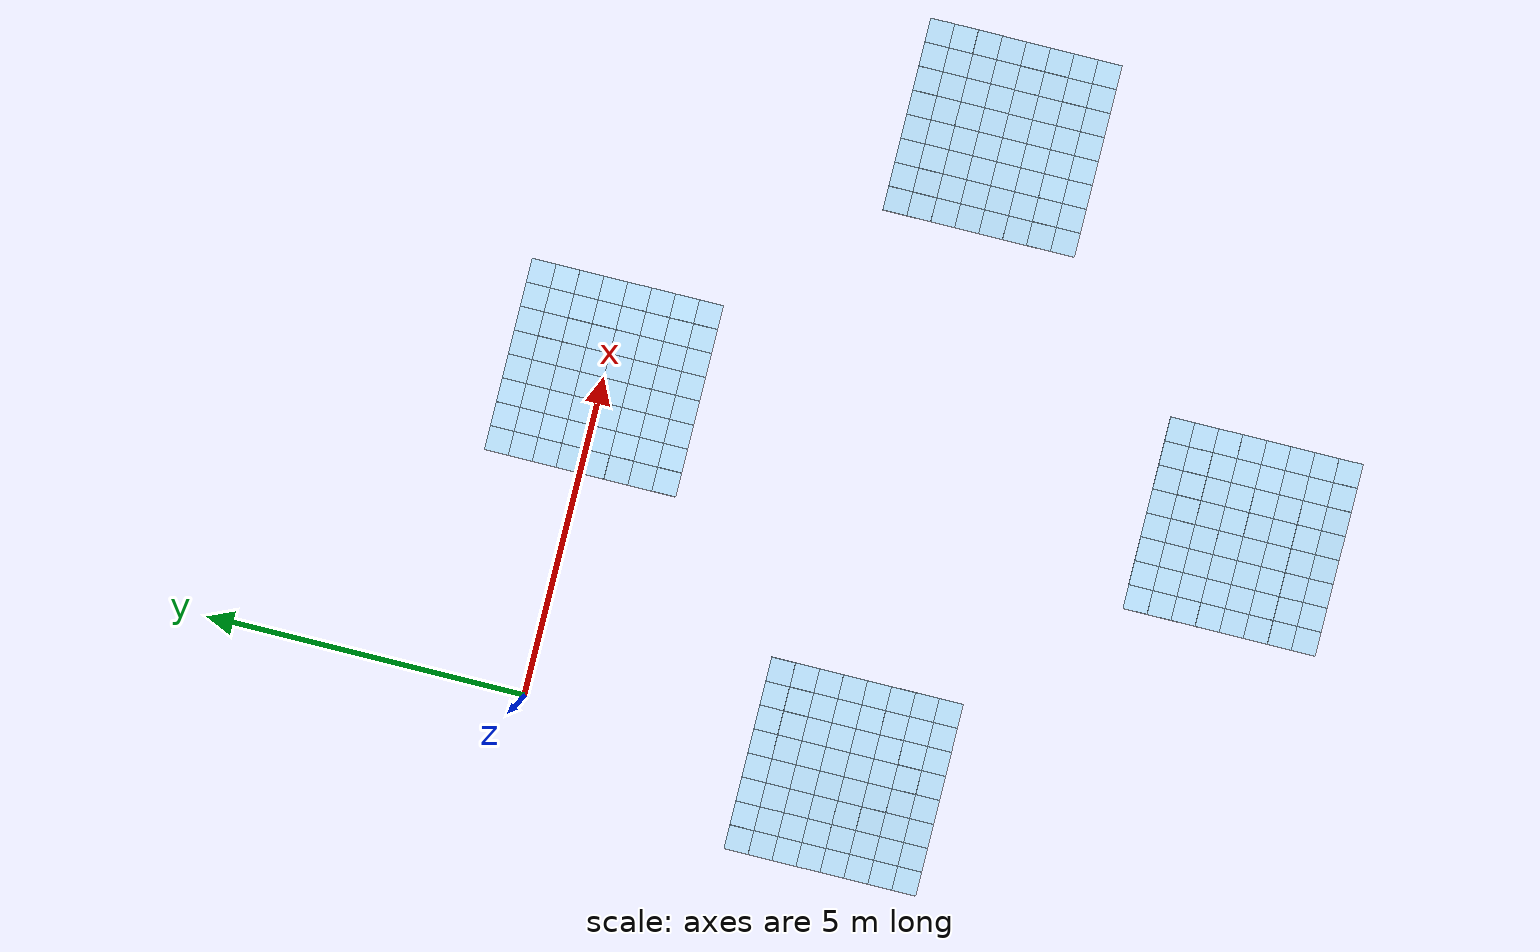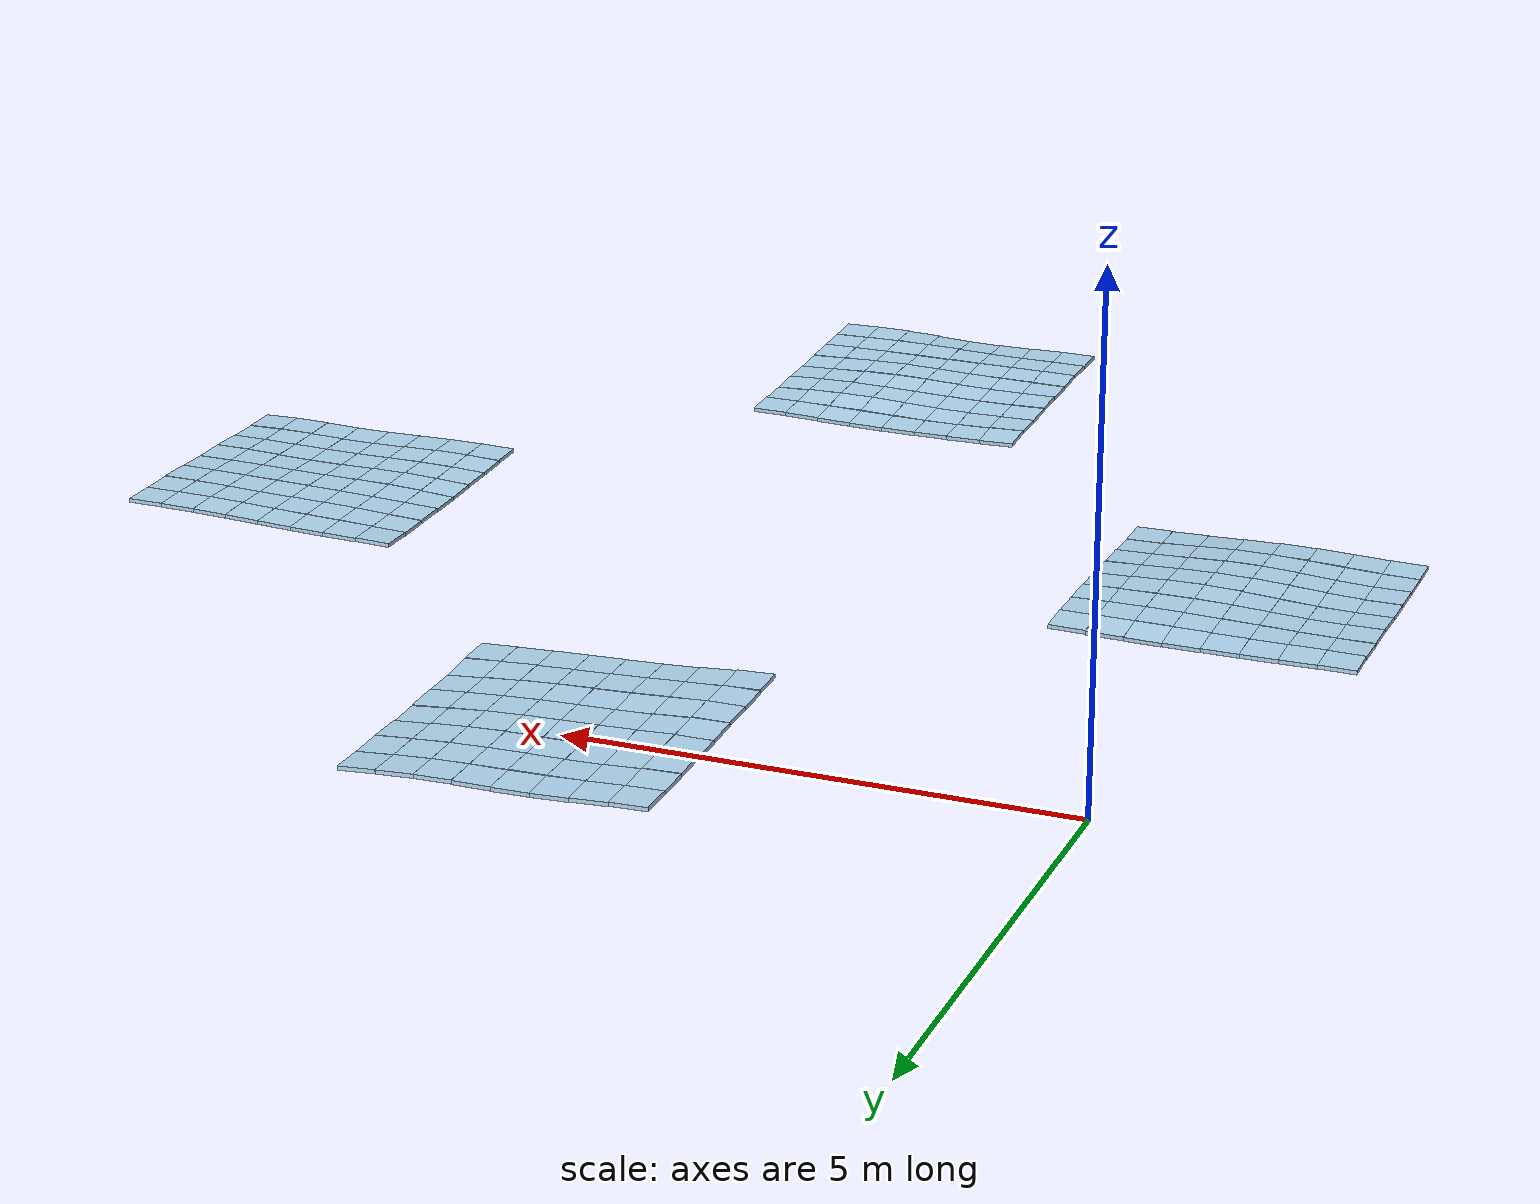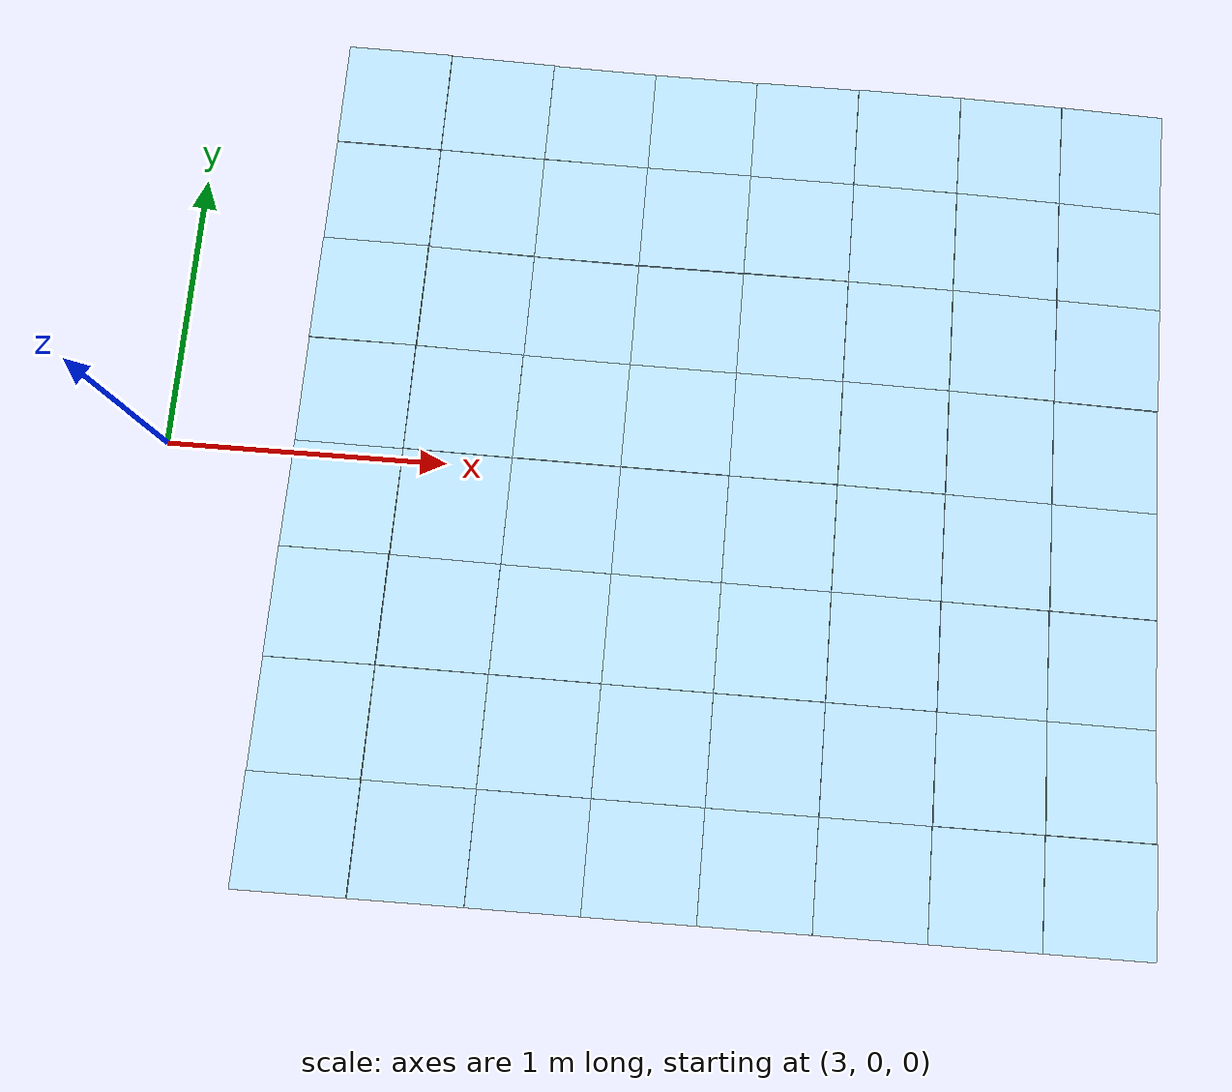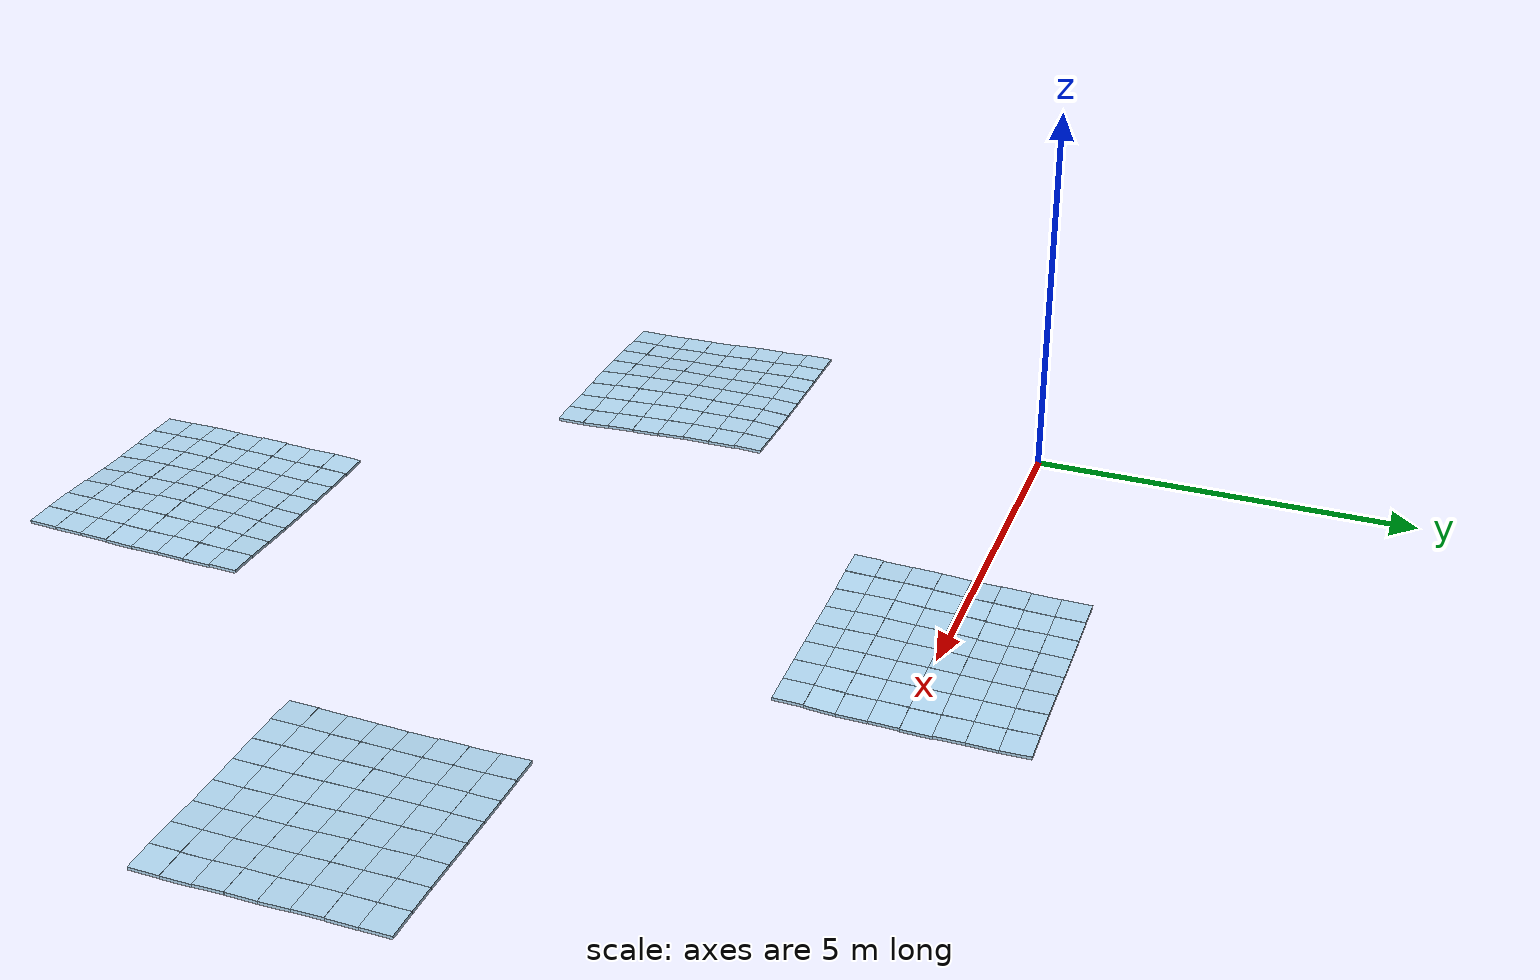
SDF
<sdf version="1.8">
 <world name="default">
  <spherical_coordinates>
   <surface_model>EARTH_WGS84</surface_model>
   <world_frame_orientation>ENU</world_frame_orientation>
   <latitude_deg>30.0444</latitude_deg>
   <longitude_deg>31.2357</longitude_deg>
   <elevation>74.0</elevation>
   <heading_deg>0</heading_deg>
  </spherical_coordinates>
  <magnetic_field>5.5645e-6 22.8758e-6 -42.3884e-6</magnetic_field>
  <physics name="1ms" type="bullet-featherstone">
   <max_step_size>0.001</max_step_size>
   <real_time_factor>1.0</real_time_factor>
  </physics>
  <plugin filename="gz-sim-physics-system" name="gz::sim::systems::Physics"/>
  <plugin filename="gz-sim-sensors-system" name="gz::sim::systems::Sensors">
   <render_engine>ogre2</render_engine>
  </plugin>
  <plugin filename="gz-sim-user-commands-system" name="gz::sim::systems::UserCommands"/>
  <plugin filename="gz-sim-scene-broadcaster-system" name="gz::sim::systems::SceneBroadcaster"/>
  <plugin filename="gz-sim-navsat-system" name="gz::sim::systems::NavSat"/>
  <plugin filename="gz-sim-magnetometer-system" name="gz::sim::systems::Magnetometer"/>
  <light type="directional" name="sun">
   <pose>0 0 10 0 0 0</pose>
   <diffuse>0.8 0.8 0.8 1</diffuse>
   <specular>0.2 0.2 0.2 1</specular>
   <attenuation>
    <range>1000</range>
    <constant>0.9</constant>
    <linear>0.01</linear>
    <quadratic>0.001</quadratic>
   </attenuation>
   <direction>-0.5 0.1 -0.9</direction>
  </light>
  <model name="slip_patch_0">
   <static>true</static>
   <link name="t_0_0">
    <pose>3.6875 -1.3125 0.2237 -0.02698 0.03791 0</pose>
    <collision name="collision">
     <geometry><box><size>0.3750 0.3750 0.04</size></box></geometry>
     <surface><friction><ode><mu>0.3</mu><mu2>0.3</mu2></ode></friction></surface>
    </collision>
    <visual name="visual">
     <geometry><box><size>0.3750 0.3750 0.04</size></box></geometry>
     <material>
      <ambient>0.62 0.76 0.85 1</ambient>
      <diffuse>0.70 0.85 0.95 1</diffuse>
      <specular>0.9 0.9 0.9 1</specular>
     </material>
    </visual>
   </link>
   <link name="t_0_1">
    <pose>3.6875 -0.9375 0.2101 -0.02581 -0.00199 0</pose>
    <collision name="collision">
     <geometry><box><size>0.3750 0.3750 0.04</size></box></geometry>
     <surface><friction><ode><mu>0.3</mu><mu2>0.3</mu2></ode></friction></surface>
    </collision>
    <visual name="visual">
     <geometry><box><size>0.3750 0.3750 0.04</size></box></geometry>
     <material>
      <ambient>0.62 0.76 0.85 1</ambient>
      <diffuse>0.70 0.85 0.95 1</diffuse>
      <specular>0.9 0.9 0.9 1</specular>
     </material>
    </visual>
   </link>
   <link name="t_0_2">
    <pose>3.6875 -0.5625 0.2039 -0.02700 -0.00079 0</pose>
    <collision name="collision">
     <geometry><box><size>0.3750 0.3750 0.04</size></box></geometry>
     <surface><friction><ode><mu>0.3</mu><mu2>0.3</mu2></ode></friction></surface>
    </collision>
    <visual name="visual">
     <geometry><box><size>0.3750 0.3750 0.04</size></box></geometry>
     <material>
      <ambient>0.62 0.76 0.85 1</ambient>
      <diffuse>0.70 0.85 0.95 1</diffuse>
      <specular>0.9 0.9 0.9 1</specular>
     </material>
    </visual>
   </link>
   <link name="t_0_3">
    <pose>3.6875 -0.1875 0.1853 -0.05277 0.00854 0</pose>
    <collision name="collision">
     <geometry><box><size>0.3750 0.3750 0.04</size></box></geometry>
     <surface><friction><ode><mu>0.3</mu><mu2>0.3</mu2></ode></friction></surface>
    </collision>
    <visual name="visual">
     <geometry><box><size>0.3750 0.3750 0.04</size></box></geometry>
     <material>
      <ambient>0.62 0.76 0.85 1</ambient>
      <diffuse>0.70 0.85 0.95 1</diffuse>
      <specular>0.9 0.9 0.9 1</specular>
     </material>
    </visual>
   </link>
   <link name="t_0_4">
    <pose>3.6875 0.1875 0.1733 -0.01191 0.00159 0</pose>
    <collision name="collision">
     <geometry><box><size>0.3750 0.3750 0.04</size></box></geometry>
     <surface><friction><ode><mu>0.3</mu><mu2>0.3</mu2></ode></friction></surface>
    </collision>
    <visual name="visual">
     <geometry><box><size>0.3750 0.3750 0.04</size></box></geometry>
     <material>
      <ambient>0.62 0.76 0.85 1</ambient>
      <diffuse>0.70 0.85 0.95 1</diffuse>
      <specular>0.9 0.9 0.9 1</specular>
     </material>
    </visual>
   </link>
   <link name="t_0_5">
    <pose>3.6875 0.5625 0.1686 -0.02680 0.02184 0</pose>
    <collision name="collision">
     <geometry><box><size>0.3750 0.3750 0.04</size></box></geometry>
     <surface><friction><ode><mu>0.3</mu><mu2>0.3</mu2></ode></friction></surface>
    </collision>
    <visual name="visual">
     <geometry><box><size>0.3750 0.3750 0.04</size></box></geometry>
     <material>
      <ambient>0.62 0.76 0.85 1</ambient>
      <diffuse>0.70 0.85 0.95 1</diffuse>
      <specular>0.9 0.9 0.9 1</specular>
     </material>
    </visual>
   </link>
   <link name="t_0_6">
    <pose>3.6875 0.9375 0.1546 -0.02481 0.02184 0</pose>
    <collision name="collision">
     <geometry><box><size>0.3750 0.3750 0.04</size></box></geometry>
     <surface><friction><ode><mu>0.3</mu><mu2>0.3</mu2></ode></friction></surface>
    </collision>
    <visual name="visual">
     <geometry><box><size>0.3750 0.3750 0.04</size></box></geometry>
     <material>
      <ambient>0.62 0.76 0.85 1</ambient>
      <diffuse>0.70 0.85 0.95 1</diffuse>
      <specular>0.9 0.9 0.9 1</specular>
     </material>
    </visual>
   </link>
   <link name="t_0_7">
    <pose>3.6875 1.3125 0.1533 -0.00119 0.02601 0</pose>
    <collision name="collision">
     <geometry><box><size>0.3750 0.3750 0.04</size></box></geometry>
     <surface><friction><ode><mu>0.3</mu><mu2>0.3</mu2></ode></friction></surface>
    </collision>
    <visual name="visual">
     <geometry><box><size>0.3750 0.3750 0.04</size></box></geometry>
     <material>
      <ambient>0.62 0.76 0.85 1</ambient>
      <diffuse>0.70 0.85 0.95 1</diffuse>
      <specular>0.9 0.9 0.9 1</specular>
     </material>
    </visual>
   </link>
   <link name="t_1_0">
    <pose>4.0625 -1.3125 0.2005 -0.00990 0.06939 0</pose>
    <collision name="collision">
     <geometry><box><size>0.3750 0.3750 0.04</size></box></geometry>
     <surface><friction><ode><mu>0.3</mu><mu2>0.3</mu2></ode></friction></surface>
    </collision>
    <visual name="visual">
     <geometry><box><size>0.3750 0.3750 0.04</size></box></geometry>
     <material>
      <ambient>0.62 0.76 0.85 1</ambient>
      <diffuse>0.70 0.85 0.95 1</diffuse>
      <specular>0.9 0.9 0.9 1</specular>
     </material>
    </visual>
   </link>
   <link name="t_1_1">
    <pose>4.0625 -0.9375 0.1983 -0.00496 0.04465 0</pose>
    <collision name="collision">
     <geometry><box><size>0.3750 0.3750 0.04</size></box></geometry>
     <surface><friction><ode><mu>0.3</mu><mu2>0.3</mu2></ode></friction></surface>
    </collision>
    <visual name="visual">
     <geometry><box><size>0.3750 0.3750 0.04</size></box></geometry>
     <material>
      <ambient>0.62 0.76 0.85 1</ambient>
      <diffuse>0.70 0.85 0.95 1</diffuse>
      <specular>0.9 0.9 0.9 1</specular>
     </material>
    </visual>
   </link>
   <link name="t_1_2">
    <pose>4.0625 -0.5625 0.1890 -0.04357 0.06346 0</pose>
    <collision name="collision">
     <geometry><box><size>0.3750 0.3750 0.04</size></box></geometry>
     <surface><friction><ode><mu>0.3</mu><mu2>0.3</mu2></ode></friction></surface>
    </collision>
    <visual name="visual">
     <geometry><box><size>0.3750 0.3750 0.04</size></box></geometry>
     <material>
      <ambient>0.62 0.76 0.85 1</ambient>
      <diffuse>0.70 0.85 0.95 1</diffuse>
      <specular>0.9 0.9 0.9 1</specular>
     </material>
    </visual>
   </link>
   <link name="t_1_3">
    <pose>4.0625 -0.1875 0.1717 -0.03271 0.05258 0</pose>
    <collision name="collision">
     <geometry><box><size>0.3750 0.3750 0.04</size></box></geometry>
     <surface><friction><ode><mu>0.3</mu><mu2>0.3</mu2></ode></friction></surface>
    </collision>
    <visual name="visual">
     <geometry><box><size>0.3750 0.3750 0.04</size></box></geometry>
     <material>
      <ambient>0.62 0.76 0.85 1</ambient>
      <diffuse>0.70 0.85 0.95 1</diffuse>
      <specular>0.9 0.9 0.9 1</specular>
     </material>
    </visual>
   </link>
   <link name="t_1_4">
    <pose>4.0625 0.1875 0.1630 -0.03173 0.04762 0</pose>
    <collision name="collision">
     <geometry><box><size>0.3750 0.3750 0.04</size></box></geometry>
     <surface><friction><ode><mu>0.3</mu><mu2>0.3</mu2></ode></friction></surface>
    </collision>
    <visual name="visual">
     <geometry><box><size>0.3750 0.3750 0.04</size></box></geometry>
     <material>
      <ambient>0.62 0.76 0.85 1</ambient>
      <diffuse>0.70 0.85 0.95 1</diffuse>
      <specular>0.9 0.9 0.9 1</specular>
     </material>
    </visual>
   </link>
   <link name="t_1_5">
    <pose>4.0625 0.5625 0.1471 -0.03860 0.07236 0</pose>
    <collision name="collision">
     <geometry><box><size>0.3750 0.3750 0.04</size></box></geometry>
     <surface><friction><ode><mu>0.3</mu><mu2>0.3</mu2></ode></friction></surface>
    </collision>
    <visual name="visual">
     <geometry><box><size>0.3750 0.3750 0.04</size></box></geometry>
     <material>
      <ambient>0.62 0.76 0.85 1</ambient>
      <diffuse>0.70 0.85 0.95 1</diffuse>
      <specular>0.9 0.9 0.9 1</specular>
     </material>
    </visual>
   </link>
   <link name="t_1_6">
    <pose>4.0625 0.9375 0.1394 -0.00992 0.04960 0</pose>
    <collision name="collision">
     <geometry><box><size>0.3750 0.3750 0.04</size></box></geometry>
     <surface><friction><ode><mu>0.3</mu><mu2>0.3</mu2></ode></friction></surface>
    </collision>
    <visual name="visual">
     <geometry><box><size>0.3750 0.3750 0.04</size></box></geometry>
     <material>
      <ambient>0.62 0.76 0.85 1</ambient>
      <diffuse>0.70 0.85 0.95 1</diffuse>
      <specular>0.9 0.9 0.9 1</specular>
     </material>
    </visual>
   </link>
   <link name="t_1_7">
    <pose>4.0625 1.3125 0.1366 -0.01190 0.04861 0</pose>
    <collision name="collision">
     <geometry><box><size>0.3750 0.3750 0.04</size></box></geometry>
     <surface><friction><ode><mu>0.3</mu><mu2>0.3</mu2></ode></friction></surface>
    </collision>
    <visual name="visual">
     <geometry><box><size>0.3750 0.3750 0.04</size></box></geometry>
     <material>
      <ambient>0.62 0.76 0.85 1</ambient>
      <diffuse>0.70 0.85 0.95 1</diffuse>
      <specular>0.9 0.9 0.9 1</specular>
     </material>
    </visual>
   </link>
   <link name="t_2_0">
    <pose>4.4375 -1.3125 0.1764 0.00516 0.05495 0</pose>
    <collision name="collision">
     <geometry><box><size>0.3750 0.3750 0.04</size></box></geometry>
     <surface><friction><ode><mu>0.3</mu><mu2>0.3</mu2></ode></friction></surface>
    </collision>
    <visual name="visual">
     <geometry><box><size>0.3750 0.3750 0.04</size></box></geometry>
     <material>
      <ambient>0.62 0.76 0.85 1</ambient>
      <diffuse>0.70 0.85 0.95 1</diffuse>
      <specular>0.9 0.9 0.9 1</specular>
     </material>
    </visual>
   </link>
   <link name="t_2_1">
    <pose>4.4375 -0.9375 0.1813 -0.00496 0.04960 0</pose>
    <collision name="collision">
     <geometry><box><size>0.3750 0.3750 0.04</size></box></geometry>
     <surface><friction><ode><mu>0.3</mu><mu2>0.3</mu2></ode></friction></surface>
    </collision>
    <visual name="visual">
     <geometry><box><size>0.3750 0.3750 0.04</size></box></geometry>
     <material>
      <ambient>0.62 0.76 0.85 1</ambient>
      <diffuse>0.70 0.85 0.95 1</diffuse>
      <specular>0.9 0.9 0.9 1</specular>
     </material>
    </visual>
   </link>
   <link name="t_2_2">
    <pose>4.4375 -0.5625 0.1667 -0.05172 0.04980 0</pose>
    <collision name="collision">
     <geometry><box><size>0.3750 0.3750 0.04</size></box></geometry>
     <surface><friction><ode><mu>0.3</mu><mu2>0.3</mu2></ode></friction></surface>
    </collision>
    <visual name="visual">
     <geometry><box><size>0.3750 0.3750 0.04</size></box></geometry>
     <material>
      <ambient>0.62 0.76 0.85 1</ambient>
      <diffuse>0.70 0.85 0.95 1</diffuse>
      <specular>0.9 0.9 0.9 1</specular>
     </material>
    </visual>
   </link>
   <link name="t_2_3">
    <pose>4.4375 -0.1875 0.1548 -0.01052 0.03434 0</pose>
    <collision name="collision">
     <geometry><box><size>0.3750 0.3750 0.04</size></box></geometry>
     <surface><friction><ode><mu>0.3</mu><mu2>0.3</mu2></ode></friction></surface>
    </collision>
    <visual name="visual">
     <geometry><box><size>0.3750 0.3750 0.04</size></box></geometry>
     <material>
      <ambient>0.62 0.76 0.85 1</ambient>
      <diffuse>0.70 0.85 0.95 1</diffuse>
      <specular>0.9 0.9 0.9 1</specular>
     </material>
    </visual>
   </link>
   <link name="t_2_4">
    <pose>4.4375 0.1875 0.1459 -0.04957 0.03672 0</pose>
    <collision name="collision">
     <geometry><box><size>0.3750 0.3750 0.04</size></box></geometry>
     <surface><friction><ode><mu>0.3</mu><mu2>0.3</mu2></ode></friction></surface>
    </collision>
    <visual name="visual">
     <geometry><box><size>0.3750 0.3750 0.04</size></box></geometry>
     <material>
      <ambient>0.62 0.76 0.85 1</ambient>
      <diffuse>0.70 0.85 0.95 1</diffuse>
      <specular>0.9 0.9 0.9 1</specular>
     </material>
    </visual>
   </link>
   <link name="t_2_5">
    <pose>4.4375 0.5625 0.1252 -0.02936 0.04267 0</pose>
    <collision name="collision">
     <geometry><box><size>0.3750 0.3750 0.04</size></box></geometry>
     <surface><friction><ode><mu>0.3</mu><mu2>0.3</mu2></ode></friction></surface>
    </collision>
    <visual name="visual">
     <geometry><box><size>0.3750 0.3750 0.04</size></box></geometry>
     <material>
      <ambient>0.62 0.76 0.85 1</ambient>
      <diffuse>0.70 0.85 0.95 1</diffuse>
      <specular>0.9 0.9 0.9 1</specular>
     </material>
    </visual>
   </link>
   <link name="t_2_6">
    <pose>4.4375 0.9375 0.1251 0.00496 0.02581 0</pose>
    <collision name="collision">
     <geometry><box><size>0.3750 0.3750 0.04</size></box></geometry>
     <surface><friction><ode><mu>0.3</mu><mu2>0.3</mu2></ode></friction></surface>
    </collision>
    <visual name="visual">
     <geometry><box><size>0.3750 0.3750 0.04</size></box></geometry>
     <material>
      <ambient>0.62 0.76 0.85 1</ambient>
      <diffuse>0.70 0.85 0.95 1</diffuse>
      <specular>0.9 0.9 0.9 1</specular>
     </material>
    </visual>
   </link>
   <link name="t_2_7">
    <pose>4.4375 1.3125 0.1189 -0.02817 0.04009 0</pose>
    <collision name="collision">
     <geometry><box><size>0.3750 0.3750 0.04</size></box></geometry>
     <surface><friction><ode><mu>0.3</mu><mu2>0.3</mu2></ode></friction></surface>
    </collision>
    <visual name="visual">
     <geometry><box><size>0.3750 0.3750 0.04</size></box></geometry>
     <material>
      <ambient>0.62 0.76 0.85 1</ambient>
      <diffuse>0.70 0.85 0.95 1</diffuse>
      <specular>0.9 0.9 0.9 1</specular>
     </material>
    </visual>
   </link>
   <link name="t_3_0">
    <pose>4.8125 -1.3125 0.1592 -0.00000 0.03870 0</pose>
    <collision name="collision">
     <geometry><box><size>0.3750 0.3750 0.04</size></box></geometry>
     <surface><friction><ode><mu>0.3</mu><mu2>0.3</mu2></ode></friction></surface>
    </collision>
    <visual name="visual">
     <geometry><box><size>0.3750 0.3750 0.04</size></box></geometry>
     <material>
      <ambient>0.62 0.76 0.85 1</ambient>
      <diffuse>0.70 0.85 0.95 1</diffuse>
      <specular>0.9 0.9 0.9 1</specular>
     </material>
    </visual>
   </link>
   <link name="t_3_1">
    <pose>4.8125 -0.9375 0.1639 -0.00099 0.04069 0</pose>
    <collision name="collision">
     <geometry><box><size>0.3750 0.3750 0.04</size></box></geometry>
     <surface><friction><ode><mu>0.3</mu><mu2>0.3</mu2></ode></friction></surface>
    </collision>
    <visual name="visual">
     <geometry><box><size>0.3750 0.3750 0.04</size></box></geometry>
     <material>
      <ambient>0.62 0.76 0.85 1</ambient>
      <diffuse>0.70 0.85 0.95 1</diffuse>
      <specular>0.9 0.9 0.9 1</specular>
     </material>
    </visual>
   </link>
   <link name="t_3_2">
    <pose>4.8125 -0.5625 0.1520 -0.03710 0.02938 0</pose>
    <collision name="collision">
     <geometry><box><size>0.3750 0.3750 0.04</size></box></geometry>
     <surface><friction><ode><mu>0.3</mu><mu2>0.3</mu2></ode></friction></surface>
    </collision>
    <visual name="visual">
     <geometry><box><size>0.3750 0.3750 0.04</size></box></geometry>
     <material>
      <ambient>0.62 0.76 0.85 1</ambient>
      <diffuse>0.70 0.85 0.95 1</diffuse>
      <specular>0.9 0.9 0.9 1</specular>
     </material>
    </visual>
   </link>
   <link name="t_3_3">
    <pose>4.8125 -0.1875 0.1447 -0.00615 0.02402 0</pose>
    <collision name="collision">
     <geometry><box><size>0.3750 0.3750 0.04</size></box></geometry>
     <surface><friction><ode><mu>0.3</mu><mu2>0.3</mu2></ode></friction></surface>
    </collision>
    <visual name="visual">
     <geometry><box><size>0.3750 0.3750 0.04</size></box></geometry>
     <material>
      <ambient>0.62 0.76 0.85 1</ambient>
      <diffuse>0.70 0.85 0.95 1</diffuse>
      <specular>0.9 0.9 0.9 1</specular>
     </material>
    </visual>
   </link>
   <link name="t_3_4">
    <pose>4.8125 0.1875 0.1353 -0.05197 0.02323 0</pose>
    <collision name="collision">
     <geometry><box><size>0.3750 0.3750 0.04</size></box></geometry>
     <surface><friction><ode><mu>0.3</mu><mu2>0.3</mu2></ode></friction></surface>
    </collision>
    <visual name="visual">
     <geometry><box><size>0.3750 0.3750 0.04</size></box></geometry>
     <material>
      <ambient>0.62 0.76 0.85 1</ambient>
      <diffuse>0.70 0.85 0.95 1</diffuse>
      <specular>0.9 0.9 0.9 1</specular>
     </material>
    </visual>
   </link>
   <link name="t_3_5">
    <pose>4.8125 0.5625 0.1161 -0.01926 0.00735 0</pose>
    <collision name="collision">
     <geometry><box><size>0.3750 0.3750 0.04</size></box></geometry>
     <surface><friction><ode><mu>0.3</mu><mu2>0.3</mu2></ode></friction></surface>
    </collision>
    <visual name="visual">
     <geometry><box><size>0.3750 0.3750 0.04</size></box></geometry>
     <material>
      <ambient>0.62 0.76 0.85 1</ambient>
      <diffuse>0.70 0.85 0.95 1</diffuse>
      <specular>0.9 0.9 0.9 1</specular>
     </material>
    </visual>
   </link>
   <link name="t_3_6">
    <pose>4.8125 0.9375 0.1195 0.00099 0.00993 0</pose>
    <collision name="collision">
     <geometry><box><size>0.3750 0.3750 0.04</size></box></geometry>
     <surface><friction><ode><mu>0.3</mu><mu2>0.3</mu2></ode></friction></surface>
    </collision>
    <visual name="visual">
     <geometry><box><size>0.3750 0.3750 0.04</size></box></geometry>
     <material>
      <ambient>0.62 0.76 0.85 1</ambient>
      <diffuse>0.70 0.85 0.95 1</diffuse>
      <specular>0.9 0.9 0.9 1</specular>
     </material>
    </visual>
   </link>
   <link name="t_3_7">
    <pose>4.8125 1.3125 0.1085 -0.02581 0.01489 0</pose>
    <collision name="collision">
     <geometry><box><size>0.3750 0.3750 0.04</size></box></geometry>
     <surface><friction><ode><mu>0.3</mu><mu2>0.3</mu2></ode></friction></surface>
    </collision>
    <visual name="visual">
     <geometry><box><size>0.3750 0.3750 0.04</size></box></geometry>
     <material>
      <ambient>0.62 0.76 0.85 1</ambient>
      <diffuse>0.70 0.85 0.95 1</diffuse>
      <specular>0.9 0.9 0.9 1</specular>
     </material>
    </visual>
   </link>
   <link name="t_4_0">
    <pose>5.1875 -1.3125 0.1458 -0.01290 0.03474 0</pose>
    <collision name="collision">
     <geometry><box><size>0.3750 0.3750 0.04</size></box></geometry>
     <surface><friction><ode><mu>0.3</mu><mu2>0.3</mu2></ode></friction></surface>
    </collision>
    <visual name="visual">
     <geometry><box><size>0.3750 0.3750 0.04</size></box></geometry>
     <material>
      <ambient>0.62 0.76 0.85 1</ambient>
      <diffuse>0.70 0.85 0.95 1</diffuse>
      <specular>0.9 0.9 0.9 1</specular>
     </material>
    </visual>
   </link>
   <link name="t_4_1">
    <pose>5.1875 -0.9375 0.1490 0.00992 0.03970 0</pose>
    <collision name="collision">
     <geometry><box><size>0.3750 0.3750 0.04</size></box></geometry>
     <surface><friction><ode><mu>0.3</mu><mu2>0.3</mu2></ode></friction></surface>
    </collision>
    <visual name="visual">
     <geometry><box><size>0.3750 0.3750 0.04</size></box></geometry>
     <material>
      <ambient>0.62 0.76 0.85 1</ambient>
      <diffuse>0.70 0.85 0.95 1</diffuse>
      <specular>0.9 0.9 0.9 1</specular>
     </material>
    </visual>
   </link>
   <link name="t_4_2">
    <pose>5.1875 -0.5625 0.1422 -0.03214 0.03137 0</pose>
    <collision name="collision">
     <geometry><box><size>0.3750 0.3750 0.04</size></box></geometry>
     <surface><friction><ode><mu>0.3</mu><mu2>0.3</mu2></ode></friction></surface>
    </collision>
    <visual name="visual">
     <geometry><box><size>0.3750 0.3750 0.04</size></box></geometry>
     <material>
      <ambient>0.62 0.76 0.85 1</ambient>
      <diffuse>0.70 0.85 0.95 1</diffuse>
      <specular>0.9 0.9 0.9 1</specular>
     </material>
    </visual>
   </link>
   <link name="t_4_3">
    <pose>5.1875 -0.1875 0.1354 -0.00596 0.02760 0</pose>
    <collision name="collision">
     <geometry><box><size>0.3750 0.3750 0.04</size></box></geometry>
     <surface><friction><ode><mu>0.3</mu><mu2>0.3</mu2></ode></friction></surface>
    </collision>
    <visual name="visual">
     <geometry><box><size>0.3750 0.3750 0.04</size></box></geometry>
     <material>
      <ambient>0.62 0.76 0.85 1</ambient>
      <diffuse>0.70 0.85 0.95 1</diffuse>
      <specular>0.9 0.9 0.9 1</specular>
     </material>
    </visual>
   </link>
   <link name="t_4_4">
    <pose>5.1875 0.1875 0.1283 -0.03374 0.01906 0</pose>
    <collision name="collision">
     <geometry><box><size>0.3750 0.3750 0.04</size></box></geometry>
     <surface><friction><ode><mu>0.3</mu><mu2>0.3</mu2></ode></friction></surface>
    </collision>
    <visual name="visual">
     <geometry><box><size>0.3750 0.3750 0.04</size></box></geometry>
     <material>
      <ambient>0.62 0.76 0.85 1</ambient>
      <diffuse>0.70 0.85 0.95 1</diffuse>
      <specular>0.9 0.9 0.9 1</specular>
     </material>
    </visual>
   </link>
   <link name="t_4_5">
    <pose>5.1875 0.5625 0.1158 -0.01569 0.00199 0</pose>
    <collision name="collision">
     <geometry><box><size>0.3750 0.3750 0.04</size></box></geometry>
     <surface><friction><ode><mu>0.3</mu><mu2>0.3</mu2></ode></friction></surface>
    </collision>
    <visual name="visual">
     <geometry><box><size>0.3750 0.3750 0.04</size></box></geometry>
     <material>
      <ambient>0.62 0.76 0.85 1</ambient>
      <diffuse>0.70 0.85 0.95 1</diffuse>
      <specular>0.9 0.9 0.9 1</specular>
     </material>
    </visual>
   </link>
   <link name="t_4_6">
    <pose>5.1875 0.9375 0.1143 -0.01390 0.01589 0</pose>
    <collision name="collision">
     <geometry><box><size>0.3750 0.3750 0.04</size></box></geometry>
     <surface><friction><ode><mu>0.3</mu><mu2>0.3</mu2></ode></friction></surface>
    </collision>
    <visual name="visual">
     <geometry><box><size>0.3750 0.3750 0.04</size></box></geometry>
     <material>
      <ambient>0.62 0.76 0.85 1</ambient>
      <diffuse>0.70 0.85 0.95 1</diffuse>
      <specular>0.9 0.9 0.9 1</specular>
     </material>
    </visual>
   </link>
   <link name="t_4_7">
    <pose>5.1875 1.3125 0.1062 -0.01092 0.00139 0</pose>
    <collision name="collision">
     <geometry><box><size>0.3750 0.3750 0.04</size></box></geometry>
     <surface><friction><ode><mu>0.3</mu><mu2>0.3</mu2></ode></friction></surface>
    </collision>
    <visual name="visual">
     <geometry><box><size>0.3750 0.3750 0.04</size></box></geometry>
     <material>
      <ambient>0.62 0.76 0.85 1</ambient>
      <diffuse>0.70 0.85 0.95 1</diffuse>
      <specular>0.9 0.9 0.9 1</specular>
     </material>
    </visual>
   </link>
   <link name="t_5_0">
    <pose>5.5625 -1.3125 0.1328 -0.01369 0.03593 0</pose>
    <collision name="collision">
     <geometry><box><size>0.3750 0.3750 0.04</size></box></geometry>
     <surface><friction><ode><mu>0.3</mu><mu2>0.3</mu2></ode></friction></surface>
    </collision>
    <visual name="visual">
     <geometry><box><size>0.3750 0.3750 0.04</size></box></geometry>
     <material>
      <ambient>0.62 0.76 0.85 1</ambient>
      <diffuse>0.70 0.85 0.95 1</diffuse>
      <specular>0.9 0.9 0.9 1</specular>
     </material>
    </visual>
   </link>
   <link name="t_5_1">
    <pose>5.5625 -0.9375 0.1332 -0.00099 0.04762 0</pose>
    <collision name="collision">
     <geometry><box><size>0.3750 0.3750 0.04</size></box></geometry>
     <surface><friction><ode><mu>0.3</mu><mu2>0.3</mu2></ode></friction></surface>
    </collision>
    <visual name="visual">
     <geometry><box><size>0.3750 0.3750 0.04</size></box></geometry>
     <material>
      <ambient>0.62 0.76 0.85 1</ambient>
      <diffuse>0.70 0.85 0.95 1</diffuse>
      <specular>0.9 0.9 0.9 1</specular>
     </material>
    </visual>
   </link>
   <link name="t_5_2">
    <pose>5.5625 -0.5625 0.1267 -0.02597 0.05357 0</pose>
    <collision name="collision">
     <geometry><box><size>0.3750 0.3750 0.04</size></box></geometry>
     <surface><friction><ode><mu>0.3</mu><mu2>0.3</mu2></ode></friction></surface>
    </collision>
    <visual name="visual">
     <geometry><box><size>0.3750 0.3750 0.04</size></box></geometry>
     <material>
      <ambient>0.62 0.76 0.85 1</ambient>
      <diffuse>0.70 0.85 0.95 1</diffuse>
      <specular>0.9 0.9 0.9 1</specular>
     </material>
    </visual>
   </link>
   <link name="t_5_3">
    <pose>5.5625 -0.1875 0.1208 -0.00595 0.05000 0</pose>
    <collision name="collision">
     <geometry><box><size>0.3750 0.3750 0.04</size></box></geometry>
     <surface><friction><ode><mu>0.3</mu><mu2>0.3</mu2></ode></friction></surface>
    </collision>
    <visual name="visual">
     <geometry><box><size>0.3750 0.3750 0.04</size></box></geometry>
     <material>
      <ambient>0.62 0.76 0.85 1</ambient>
      <diffuse>0.70 0.85 0.95 1</diffuse>
      <specular>0.9 0.9 0.9 1</specular>
     </material>
    </visual>
   </link>
   <link name="t_5_4">
    <pose>5.5625 0.1875 0.1169 -0.01785 0.04762 0</pose>
    <collision name="collision">
     <geometry><box><size>0.3750 0.3750 0.04</size></box></geometry>
     <surface><friction><ode><mu>0.3</mu><mu2>0.3</mu2></ode></friction></surface>
    </collision>
    <visual name="visual">
     <geometry><box><size>0.3750 0.3750 0.04</size></box></geometry>
     <material>
      <ambient>0.62 0.76 0.85 1</ambient>
      <diffuse>0.70 0.85 0.95 1</diffuse>
      <specular>0.9 0.9 0.9 1</specular>
     </material>
    </visual>
   </link>
   <link name="t_5_5">
    <pose>5.5625 0.5625 0.1095 -0.01389 0.03394 0</pose>
    <collision name="collision">
     <geometry><box><size>0.3750 0.3750 0.04</size></box></geometry>
     <surface><friction><ode><mu>0.3</mu><mu2>0.3</mu2></ode></friction></surface>
    </collision>
    <visual name="visual">
     <geometry><box><size>0.3750 0.3750 0.04</size></box></geometry>
     <material>
      <ambient>0.62 0.76 0.85 1</ambient>
      <diffuse>0.70 0.85 0.95 1</diffuse>
      <specular>0.9 0.9 0.9 1</specular>
     </material>
    </visual>
   </link>
   <link name="t_5_6">
    <pose>5.5625 0.9375 0.1056 -0.00992 0.03275 0</pose>
    <collision name="collision">
     <geometry><box><size>0.3750 0.3750 0.04</size></box></geometry>
     <surface><friction><ode><mu>0.3</mu><mu2>0.3</mu2></ode></friction></surface>
    </collision>
    <visual name="visual">
     <geometry><box><size>0.3750 0.3750 0.04</size></box></geometry>
     <material>
      <ambient>0.62 0.76 0.85 1</ambient>
      <diffuse>0.70 0.85 0.95 1</diffuse>
      <specular>0.9 0.9 0.9 1</specular>
     </material>
    </visual>
   </link>
   <link name="t_5_7">
    <pose>5.5625 1.3125 0.1038 0.00377 0.01986 0</pose>
    <collision name="collision">
     <geometry><box><size>0.3750 0.3750 0.04</size></box></geometry>
     <surface><friction><ode><mu>0.3</mu><mu2>0.3</mu2></ode></friction></surface>
    </collision>
    <visual name="visual">
     <geometry><box><size>0.3750 0.3750 0.04</size></box></geometry>
     <material>
      <ambient>0.62 0.76 0.85 1</ambient>
      <diffuse>0.70 0.85 0.95 1</diffuse>
      <specular>0.9 0.9 0.9 1</specular>
     </material>
    </visual>
   </link>
   <link name="t_6_0">
    <pose>5.9375 -1.3125 0.1183 -0.00694 0.04168 0</pose>
    <collision name="collision">
     <geometry><box><size>0.3750 0.3750 0.04</size></box></geometry>
     <surface><friction><ode><mu>0.3</mu><mu2>0.3</mu2></ode></friction></surface>
    </collision>
    <visual name="visual">
     <geometry><box><size>0.3750 0.3750 0.04</size></box></geometry>
     <material>
      <ambient>0.62 0.76 0.85 1</ambient>
      <diffuse>0.70 0.85 0.95 1</diffuse>
      <specular>0.9 0.9 0.9 1</specular>
     </material>
    </visual>
   </link>
   <link name="t_6_1">
    <pose>5.9375 -0.9375 0.1130 -0.03467 0.06445 0</pose>
    <collision name="collision">
     <geometry><box><size>0.3750 0.3750 0.04</size></box></geometry>
     <surface><friction><ode><mu>0.3</mu><mu2>0.3</mu2></ode></friction></surface>
    </collision>
    <visual name="visual">
     <geometry><box><size>0.3750 0.3750 0.04</size></box></geometry>
     <material>
      <ambient>0.62 0.76 0.85 1</ambient>
      <diffuse>0.70 0.85 0.95 1</diffuse>
      <specular>0.9 0.9 0.9 1</specular>
     </material>
    </visual>
   </link>
   <link name="t_6_2">
    <pose>5.9375 -0.5625 0.1009 -0.01880 0.08025 0</pose>
    <collision name="collision">
     <geometry><box><size>0.3750 0.3750 0.04</size></box></geometry>
     <surface><friction><ode><mu>0.3</mu><mu2>0.3</mu2></ode></friction></surface>
    </collision>
    <visual name="visual">
     <geometry><box><size>0.3750 0.3750 0.04</size></box></geometry>
     <material>
      <ambient>0.62 0.76 0.85 1</ambient>
      <diffuse>0.70 0.85 0.95 1</diffuse>
      <specular>0.9 0.9 0.9 1</specular>
     </material>
    </visual>
   </link>
   <link name="t_6_3">
    <pose>5.9375 -0.1875 0.0990 -0.00793 0.06544 0</pose>
    <collision name="collision">
     <geometry><box><size>0.3750 0.3750 0.04</size></box></geometry>
     <surface><friction><ode><mu>0.3</mu><mu2>0.3</mu2></ode></friction></surface>
    </collision>
    <visual name="visual">
     <geometry><box><size>0.3750 0.3750 0.04</size></box></geometry>
     <material>
      <ambient>0.62 0.76 0.85 1</ambient>
      <diffuse>0.70 0.85 0.95 1</diffuse>
      <specular>0.9 0.9 0.9 1</specular>
     </material>
    </visual>
   </link>
   <link name="t_6_4">
    <pose>5.9375 0.1875 0.0925 -0.01286 0.08321 0</pose>
    <collision name="collision">
     <geometry><box><size>0.3750 0.3750 0.04</size></box></geometry>
     <surface><friction><ode><mu>0.3</mu><mu2>0.3</mu2></ode></friction></surface>
    </collision>
    <visual name="visual">
     <geometry><box><size>0.3750 0.3750 0.04</size></box></geometry>
     <material>
      <ambient>0.62 0.76 0.85 1</ambient>
      <diffuse>0.70 0.85 0.95 1</diffuse>
      <specular>0.9 0.9 0.9 1</specular>
     </material>
    </visual>
   </link>
   <link name="t_6_5">
    <pose>5.9375 0.5625 0.0913 -0.00297 0.06643 0</pose>
    <collision name="collision">
     <geometry><box><size>0.3750 0.3750 0.04</size></box></geometry>
     <surface><friction><ode><mu>0.3</mu><mu2>0.3</mu2></ode></friction></surface>
    </collision>
    <visual name="visual">
     <geometry><box><size>0.3750 0.3750 0.04</size></box></geometry>
     <material>
      <ambient>0.62 0.76 0.85 1</ambient>
      <diffuse>0.70 0.85 0.95 1</diffuse>
      <specular>0.9 0.9 0.9 1</specular>
     </material>
    </visual>
   </link>
   <link name="t_6_6">
    <pose>5.9375 0.9375 0.0882 -0.00496 0.05950 0</pose>
    <collision name="collision">
     <geometry><box><size>0.3750 0.3750 0.04</size></box></geometry>
     <surface><friction><ode><mu>0.3</mu><mu2>0.3</mu2></ode></friction></surface>
    </collision>
    <visual name="visual">
     <geometry><box><size>0.3750 0.3750 0.04</size></box></geometry>
     <material>
      <ambient>0.62 0.76 0.85 1</ambient>
      <diffuse>0.70 0.85 0.95 1</diffuse>
      <specular>0.9 0.9 0.9 1</specular>
     </material>
    </visual>
   </link>
   <link name="t_6_7">
    <pose>5.9375 1.3125 0.0894 0.01388 0.05258 0</pose>
    <collision name="collision">
     <geometry><box><size>0.3750 0.3750 0.04</size></box></geometry>
     <surface><friction><ode><mu>0.3</mu><mu2>0.3</mu2></ode></friction></surface>
    </collision>
    <visual name="visual">
     <geometry><box><size>0.3750 0.3750 0.04</size></box></geometry>
     <material>
      <ambient>0.62 0.76 0.85 1</ambient>
      <diffuse>0.70 0.85 0.95 1</diffuse>
      <specular>0.9 0.9 0.9 1</specular>
     </material>
    </visual>
   </link>
   <link name="t_7_0">
    <pose>6.3125 -1.3125 0.1022 -0.01111 0.04782 0</pose>
    <collision name="collision">
     <geometry><box><size>0.3750 0.3750 0.04</size></box></geometry>
     <surface><friction><ode><mu>0.3</mu><mu2>0.3</mu2></ode></friction></surface>
    </collision>
    <visual name="visual">
     <geometry><box><size>0.3750 0.3750 0.04</size></box></geometry>
     <material>
      <ambient>0.62 0.76 0.85 1</ambient>
      <diffuse>0.70 0.85 0.95 1</diffuse>
      <specular>0.9 0.9 0.9 1</specular>
     </material>
    </visual>
   </link>
   <link name="t_7_1">
    <pose>6.3125 -0.9375 0.0848 -0.06327 0.07729 0</pose>
    <collision name="collision">
     <geometry><box><size>0.3750 0.3750 0.04</size></box></geometry>
     <surface><friction><ode><mu>0.3</mu><mu2>0.3</mu2></ode></friction></surface>
    </collision>
    <visual name="visual">
     <geometry><box><size>0.3750 0.3750 0.04</size></box></geometry>
     <material>
      <ambient>0.62 0.76 0.85 1</ambient>
      <diffuse>0.70 0.85 0.95 1</diffuse>
      <specular>0.9 0.9 0.9 1</specular>
     </material>
    </visual>
   </link>
   <link name="t_7_2">
    <pose>6.3125 -0.5625 0.0711 -0.00495 0.07334 0</pose>
    <collision name="collision">
     <geometry><box><size>0.3750 0.3750 0.04</size></box></geometry>
     <surface><friction><ode><mu>0.3</mu><mu2>0.3</mu2></ode></friction></surface>
    </collision>
    <visual name="visual">
     <geometry><box><size>0.3750 0.3750 0.04</size></box></geometry>
     <material>
      <ambient>0.62 0.76 0.85 1</ambient>
      <diffuse>0.70 0.85 0.95 1</diffuse>
      <specular>0.9 0.9 0.9 1</specular>
     </material>
    </visual>
   </link>
   <link name="t_7_3">
    <pose>6.3125 -0.1875 0.0712 -0.02336 0.07532 0</pose>
    <collision name="collision">
     <geometry><box><size>0.3750 0.3750 0.04</size></box></geometry>
     <surface><friction><ode><mu>0.3</mu><mu2>0.3</mu2></ode></friction></surface>
    </collision>
    <visual name="visual">
     <geometry><box><size>0.3750 0.3750 0.04</size></box></geometry>
     <material>
      <ambient>0.62 0.76 0.85 1</ambient>
      <diffuse>0.70 0.85 0.95 1</diffuse>
      <specular>0.9 0.9 0.9 1</specular>
     </material>
    </visual>
   </link>
   <link name="t_7_4">
    <pose>6.3125 0.1875 0.0575 -0.01740 0.09129 0</pose>
    <collision name="collision">
     <geometry><box><size>0.3750 0.3750 0.04</size></box></geometry>
     <surface><friction><ode><mu>0.3</mu><mu2>0.3</mu2></ode></friction></surface>
    </collision>
    <visual name="visual">
     <geometry><box><size>0.3750 0.3750 0.04</size></box></geometry>
     <material>
      <ambient>0.62 0.76 0.85 1</ambient>
      <diffuse>0.70 0.85 0.95 1</diffuse>
      <specular>0.9 0.9 0.9 1</specular>
     </material>
    </visual>
   </link>
   <link name="t_7_5">
    <pose>6.3125 0.5625 0.0637 0.01862 0.07255 0</pose>
    <collision name="collision">
     <geometry><box><size>0.3750 0.3750 0.04</size></box></geometry>
     <surface><friction><ode><mu>0.3</mu><mu2>0.3</mu2></ode></friction></surface>
    </collision>
    <visual name="visual">
     <geometry><box><size>0.3750 0.3750 0.04</size></box></geometry>
     <material>
      <ambient>0.62 0.76 0.85 1</ambient>
      <diffuse>0.70 0.85 0.95 1</diffuse>
      <specular>0.9 0.9 0.9 1</specular>
     </material>
    </visual>
   </link>
   <link name="t_7_6">
    <pose>6.3125 0.9375 0.0631 -0.01188 0.07433 0</pose>
    <collision name="collision">
     <geometry><box><size>0.3750 0.3750 0.04</size></box></geometry>
     <surface><friction><ode><mu>0.3</mu><mu2>0.3</mu2></ode></friction></surface>
    </collision>
    <visual name="visual">
     <geometry><box><size>0.3750 0.3750 0.04</size></box></geometry>
     <material>
      <ambient>0.62 0.76 0.85 1</ambient>
      <diffuse>0.70 0.85 0.95 1</diffuse>
      <specular>0.9 0.9 0.9 1</specular>
     </material>
    </visual>
   </link>
   <link name="t_7_7">
    <pose>6.3125 1.3125 0.0654 0.02852 0.06840 0</pose>
    <collision name="collision">
     <geometry><box><size>0.3750 0.3750 0.04</size></box></geometry>
     <surface><friction><ode><mu>0.3</mu><mu2>0.3</mu2></ode></friction></surface>
    </collision>
    <visual name="visual">
     <geometry><box><size>0.3750 0.3750 0.04</size></box></geometry>
     <material>
      <ambient>0.62 0.76 0.85 1</ambient>
      <diffuse>0.70 0.85 0.95 1</diffuse>
      <specular>0.9 0.9 0.9 1</specular>
     </material>
    </visual>
   </link>
  </model>
  <model name="slip_patch_1">
   <static>true</static>
   <link name="t_0_0">
    <pose>8.6875 -6.3125 0.1632 -0.01806 -0.02700 0</pose>
    <collision name="collision">
     <geometry><box><size>0.3750 0.3750 0.04</size></box></geometry>
     <surface><friction><ode><mu>0.3</mu><mu2>0.3</mu2></ode></friction></surface>
    </collision>
    <visual name="visual">
     <geometry><box><size>0.3750 0.3750 0.04</size></box></geometry>
     <material>
      <ambient>0.62 0.76 0.85 1</ambient>
      <diffuse>0.70 0.85 0.95 1</diffuse>
      <specular>0.9 0.9 0.9 1</specular>
     </material>
    </visual>
   </link>
   <link name="t_0_1">
    <pose>8.6875 -5.9375 0.1518 -0.03470 -0.04861 0</pose>
    <collision name="collision">
     <geometry><box><size>0.3750 0.3750 0.04</size></box></geometry>
     <surface><friction><ode><mu>0.3</mu><mu2>0.3</mu2></ode></friction></surface>
    </collision>
    <visual name="visual">
     <geometry><box><size>0.3750 0.3750 0.04</size></box></geometry>
     <material>
      <ambient>0.62 0.76 0.85 1</ambient>
      <diffuse>0.70 0.85 0.95 1</diffuse>
      <specular>0.9 0.9 0.9 1</specular>
     </material>
    </visual>
   </link>
   <link name="t_0_2">
    <pose>8.6875 -5.5625 0.1428 -0.02063 -0.04782 0</pose>
    <collision name="collision">
     <geometry><box><size>0.3750 0.3750 0.04</size></box></geometry>
     <surface><friction><ode><mu>0.3</mu><mu2>0.3</mu2></ode></friction></surface>
    </collision>
    <visual name="visual">
     <geometry><box><size>0.3750 0.3750 0.04</size></box></geometry>
     <material>
      <ambient>0.62 0.76 0.85 1</ambient>
      <diffuse>0.70 0.85 0.95 1</diffuse>
      <specular>0.9 0.9 0.9 1</specular>
     </material>
    </visual>
   </link>
   <link name="t_0_3">
    <pose>8.6875 -5.1875 0.1330 -0.03111 -0.06247 0</pose>
    <collision name="collision">
     <geometry><box><size>0.3750 0.3750 0.04</size></box></geometry>
     <surface><friction><ode><mu>0.3</mu><mu2>0.3</mu2></ode></friction></surface>
    </collision>
    <visual name="visual">
     <geometry><box><size>0.3750 0.3750 0.04</size></box></geometry>
     <material>
      <ambient>0.62 0.76 0.85 1</ambient>
      <diffuse>0.70 0.85 0.95 1</diffuse>
      <specular>0.9 0.9 0.9 1</specular>
     </material>
    </visual>
   </link>
   <link name="t_0_4">
    <pose>8.6875 -4.8125 0.1257 -0.00396 -0.06405 0</pose>
    <collision name="collision">
     <geometry><box><size>0.3750 0.3750 0.04</size></box></geometry>
     <surface><friction><ode><mu>0.3</mu><mu2>0.3</mu2></ode></friction></surface>
    </collision>
    <visual name="visual">
     <geometry><box><size>0.3750 0.3750 0.04</size></box></geometry>
     <material>
      <ambient>0.62 0.76 0.85 1</ambient>
      <diffuse>0.70 0.85 0.95 1</diffuse>
      <specular>0.9 0.9 0.9 1</specular>
     </material>
    </visual>
   </link>
   <link name="t_0_5">
    <pose>8.6875 -4.4375 0.1264 -0.00694 -0.04168 0</pose>
    <collision name="collision">
     <geometry><box><size>0.3750 0.3750 0.04</size></box></geometry>
     <surface><friction><ode><mu>0.3</mu><mu2>0.3</mu2></ode></friction></surface>
    </collision>
    <visual name="visual">
     <geometry><box><size>0.3750 0.3750 0.04</size></box></geometry>
     <material>
      <ambient>0.62 0.76 0.85 1</ambient>
      <diffuse>0.70 0.85 0.95 1</diffuse>
      <specular>0.9 0.9 0.9 1</specular>
     </material>
    </visual>
   </link>
   <link name="t_0_6">
    <pose>8.6875 -4.0625 0.1208 -0.00694 -0.04960 0</pose>
    <collision name="collision">
     <geometry><box><size>0.3750 0.3750 0.04</size></box></geometry>
     <surface><friction><ode><mu>0.3</mu><mu2>0.3</mu2></ode></friction></surface>
    </collision>
    <visual name="visual">
     <geometry><box><size>0.3750 0.3750 0.04</size></box></geometry>
     <material>
      <ambient>0.62 0.76 0.85 1</ambient>
      <diffuse>0.70 0.85 0.95 1</diffuse>
      <specular>0.9 0.9 0.9 1</specular>
     </material>
    </visual>
   </link>
   <link name="t_0_7">
    <pose>8.6875 -3.6875 0.1260 0.01786 -0.03454 0</pose>
    <collision name="collision">
     <geometry><box><size>0.3750 0.3750 0.04</size></box></geometry>
     <surface><friction><ode><mu>0.3</mu><mu2>0.3</mu2></ode></friction></surface>
    </collision>
    <visual name="visual">
     <geometry><box><size>0.3750 0.3750 0.04</size></box></geometry>
     <material>
      <ambient>0.62 0.76 0.85 1</ambient>
      <diffuse>0.70 0.85 0.95 1</diffuse>
      <specular>0.9 0.9 0.9 1</specular>
     </material>
    </visual>
   </link>
   <link name="t_1_0">
    <pose>9.0625 -6.3125 0.1704 -0.00298 -0.00496 0</pose>
    <collision name="collision">
     <geometry><box><size>0.3750 0.3750 0.04</size></box></geometry>
     <surface><friction><ode><mu>0.3</mu><mu2>0.3</mu2></ode></friction></surface>
    </collision>
    <visual name="visual">
     <geometry><box><size>0.3750 0.3750 0.04</size></box></geometry>
     <material>
      <ambient>0.62 0.76 0.85 1</ambient>
      <diffuse>0.70 0.85 0.95 1</diffuse>
      <specular>0.9 0.9 0.9 1</specular>
     </material>
    </visual>
   </link>
   <link name="t_1_1">
    <pose>9.0625 -5.9375 0.1658 -0.02978 -0.01489 0</pose>
    <collision name="collision">
     <geometry><box><size>0.3750 0.3750 0.04</size></box></geometry>
     <surface><friction><ode><mu>0.3</mu><mu2>0.3</mu2></ode></friction></surface>
    </collision>
    <visual name="visual">
     <geometry><box><size>0.3750 0.3750 0.04</size></box></geometry>
     <material>
      <ambient>0.62 0.76 0.85 1</ambient>
      <diffuse>0.70 0.85 0.95 1</diffuse>
      <specular>0.9 0.9 0.9 1</specular>
     </material>
    </visual>
   </link>
   <link name="t_1_2">
    <pose>9.0625 -5.5625 0.1565 -0.00596 -0.02383 0</pose>
    <collision name="collision">
     <geometry><box><size>0.3750 0.3750 0.04</size></box></geometry>
     <surface><friction><ode><mu>0.3</mu><mu2>0.3</mu2></ode></friction></surface>
    </collision>
    <visual name="visual">
     <geometry><box><size>0.3750 0.3750 0.04</size></box></geometry>
     <material>
      <ambient>0.62 0.76 0.85 1</ambient>
      <diffuse>0.70 0.85 0.95 1</diffuse>
      <specular>0.9 0.9 0.9 1</specular>
     </material>
    </visual>
   </link>
   <link name="t_1_3">
    <pose>9.0625 -5.1875 0.1552 -0.01289 -0.04762 0</pose>
    <collision name="collision">
     <geometry><box><size>0.3750 0.3750 0.04</size></box></geometry>
     <surface><friction><ode><mu>0.3</mu><mu2>0.3</mu2></ode></friction></surface>
    </collision>
    <visual name="visual">
     <geometry><box><size>0.3750 0.3750 0.04</size></box></geometry>
     <material>
      <ambient>0.62 0.76 0.85 1</ambient>
      <diffuse>0.70 0.85 0.95 1</diffuse>
      <specular>0.9 0.9 0.9 1</specular>
     </material>
    </visual>
   </link>
   <link name="t_1_4">
    <pose>9.0625 -4.8125 0.1465 -0.02281 -0.04366 0</pose>
    <collision name="collision">
     <geometry><box><size>0.3750 0.3750 0.04</size></box></geometry>
     <surface><friction><ode><mu>0.3</mu><mu2>0.3</mu2></ode></friction></surface>
    </collision>
    <visual name="visual">
     <geometry><box><size>0.3750 0.3750 0.04</size></box></geometry>
     <material>
      <ambient>0.62 0.76 0.85 1</ambient>
      <diffuse>0.70 0.85 0.95 1</diffuse>
      <specular>0.9 0.9 0.9 1</specular>
     </material>
    </visual>
   </link>
   <link name="t_1_5">
    <pose>9.0625 -4.4375 0.1425 -0.00198 -0.04267 0</pose>
    <collision name="collision">
     <geometry><box><size>0.3750 0.3750 0.04</size></box></geometry>
     <surface><friction><ode><mu>0.3</mu><mu2>0.3</mu2></ode></friction></surface>
    </collision>
    <visual name="visual">
     <geometry><box><size>0.3750 0.3750 0.04</size></box></geometry>
     <material>
      <ambient>0.62 0.76 0.85 1</ambient>
      <diffuse>0.70 0.85 0.95 1</diffuse>
      <specular>0.9 0.9 0.9 1</specular>
     </material>
    </visual>
   </link>
   <link name="t_1_6">
    <pose>9.0625 -4.0625 0.1409 -0.00991 -0.05456 0</pose>
    <collision name="collision">
     <geometry><box><size>0.3750 0.3750 0.04</size></box></geometry>
     <surface><friction><ode><mu>0.3</mu><mu2>0.3</mu2></ode></friction></surface>
    </collision>
    <visual name="visual">
     <geometry><box><size>0.3750 0.3750 0.04</size></box></geometry>
     <material>
      <ambient>0.62 0.76 0.85 1</ambient>
      <diffuse>0.70 0.85 0.95 1</diffuse>
      <specular>0.9 0.9 0.9 1</specular>
     </material>
    </visual>
   </link>
   <link name="t_1_7">
    <pose>9.0625 -3.6875 0.1372 -0.00992 -0.02779 0</pose>
    <collision name="collision">
     <geometry><box><size>0.3750 0.3750 0.04</size></box></geometry>
     <surface><friction><ode><mu>0.3</mu><mu2>0.3</mu2></ode></friction></surface>
    </collision>
    <visual name="visual">
     <geometry><box><size>0.3750 0.3750 0.04</size></box></geometry>
     <material>
      <ambient>0.62 0.76 0.85 1</ambient>
      <diffuse>0.70 0.85 0.95 1</diffuse>
      <specular>0.9 0.9 0.9 1</specular>
     </material>
    </visual>
   </link>
   <link name="t_2_0">
    <pose>9.4375 -6.3125 0.1679 -0.00695 0.01608 0</pose>
    <collision name="collision">
     <geometry><box><size>0.3750 0.3750 0.04</size></box></geometry>
     <surface><friction><ode><mu>0.3</mu><mu2>0.3</mu2></ode></friction></surface>
    </collision>
    <visual name="visual">
     <geometry><box><size>0.3750 0.3750 0.04</size></box></geometry>
     <material>
      <ambient>0.62 0.76 0.85 1</ambient>
      <diffuse>0.70 0.85 0.95 1</diffuse>
      <specular>0.9 0.9 0.9 1</specular>
     </material>
    </visual>
   </link>
   <link name="t_2_1">
    <pose>9.4375 -5.9375 0.1645 -0.01291 0.01390 0</pose>
    <collision name="collision">
     <geometry><box><size>0.3750 0.3750 0.04</size></box></geometry>
     <surface><friction><ode><mu>0.3</mu><mu2>0.3</mu2></ode></friction></surface>
    </collision>
    <visual name="visual">
     <geometry><box><size>0.3750 0.3750 0.04</size></box></geometry>
     <material>
      <ambient>0.62 0.76 0.85 1</ambient>
      <diffuse>0.70 0.85 0.95 1</diffuse>
      <specular>0.9 0.9 0.9 1</specular>
     </material>
    </visual>
   </link>
   <link name="t_2_2">
    <pose>9.4375 -5.5625 0.1614 0.00218 -0.00298 0</pose>
    <collision name="collision">
     <geometry><box><size>0.3750 0.3750 0.04</size></box></geometry>
     <surface><friction><ode><mu>0.3</mu><mu2>0.3</mu2></ode></friction></surface>
    </collision>
    <visual name="visual">
     <geometry><box><size>0.3750 0.3750 0.04</size></box></geometry>
     <material>
      <ambient>0.62 0.76 0.85 1</ambient>
      <diffuse>0.70 0.85 0.95 1</diffuse>
      <specular>0.9 0.9 0.9 1</specular>
     </material>
    </visual>
   </link>
   <link name="t_2_3">
    <pose>9.4375 -5.1875 0.1640 -0.00079 -0.00596 0</pose>
    <collision name="collision">
     <geometry><box><size>0.3750 0.3750 0.04</size></box></geometry>
     <surface><friction><ode><mu>0.3</mu><mu2>0.3</mu2></ode></friction></surface>
    </collision>
    <visual name="visual">
     <geometry><box><size>0.3750 0.3750 0.04</size></box></geometry>
     <material>
      <ambient>0.62 0.76 0.85 1</ambient>
      <diffuse>0.70 0.85 0.95 1</diffuse>
      <specular>0.9 0.9 0.9 1</specular>
     </material>
    </visual>
   </link>
   <link name="t_2_4">
    <pose>9.4375 -4.8125 0.1587 -0.01588 -0.02422 0</pose>
    <collision name="collision">
     <geometry><box><size>0.3750 0.3750 0.04</size></box></geometry>
     <surface><friction><ode><mu>0.3</mu><mu2>0.3</mu2></ode></friction></surface>
    </collision>
    <visual name="visual">
     <geometry><box><size>0.3750 0.3750 0.04</size></box></geometry>
     <material>
      <ambient>0.62 0.76 0.85 1</ambient>
      <diffuse>0.70 0.85 0.95 1</diffuse>
      <specular>0.9 0.9 0.9 1</specular>
     </material>
    </visual>
   </link>
   <link name="t_2_5">
    <pose>9.4375 -4.4375 0.1571 0.00377 -0.03454 0</pose>
    <collision name="collision">
     <geometry><box><size>0.3750 0.3750 0.04</size></box></geometry>
     <surface><friction><ode><mu>0.3</mu><mu2>0.3</mu2></ode></friction></surface>
    </collision>
    <visual name="visual">
     <geometry><box><size>0.3750 0.3750 0.04</size></box></geometry>
     <material>
      <ambient>0.62 0.76 0.85 1</ambient>
      <diffuse>0.70 0.85 0.95 1</diffuse>
      <specular>0.9 0.9 0.9 1</specular>
     </material>
    </visual>
   </link>
   <link name="t_2_6">
    <pose>9.4375 -4.0625 0.1568 -0.01488 -0.03275 0</pose>
    <collision name="collision">
     <geometry><box><size>0.3750 0.3750 0.04</size></box></geometry>
     <surface><friction><ode><mu>0.3</mu><mu2>0.3</mu2></ode></friction></surface>
    </collision>
    <visual name="visual">
     <geometry><box><size>0.3750 0.3750 0.04</size></box></geometry>
     <material>
      <ambient>0.62 0.76 0.85 1</ambient>
      <diffuse>0.70 0.85 0.95 1</diffuse>
      <specular>0.9 0.9 0.9 1</specular>
     </material>
    </visual>
   </link>
   <link name="t_2_7">
    <pose>9.4375 -3.6875 0.1484 -0.01846 -0.03355 0</pose>
    <collision name="collision">
     <geometry><box><size>0.3750 0.3750 0.04</size></box></geometry>
     <surface><friction><ode><mu>0.3</mu><mu2>0.3</mu2></ode></friction></surface>
    </collision>
    <visual name="visual">
     <geometry><box><size>0.3750 0.3750 0.04</size></box></geometry>
     <material>
      <ambient>0.62 0.76 0.85 1</ambient>
      <diffuse>0.70 0.85 0.95 1</diffuse>
      <specular>0.9 0.9 0.9 1</specular>
     </material>
    </visual>
   </link>
   <link name="t_3_0">
    <pose>9.8125 -6.3125 0.1599 -0.02005 0.01886 0</pose>
    <collision name="collision">
     <geometry><box><size>0.3750 0.3750 0.04</size></box></geometry>
     <surface><friction><ode><mu>0.3</mu><mu2>0.3</mu2></ode></friction></surface>
    </collision>
    <visual name="visual">
     <geometry><box><size>0.3750 0.3750 0.04</size></box></geometry>
     <material>
      <ambient>0.62 0.76 0.85 1</ambient>
      <diffuse>0.70 0.85 0.95 1</diffuse>
      <specular>0.9 0.9 0.9 1</specular>
     </material>
    </visual>
   </link>
   <link name="t_3_1">
    <pose>9.8125 -5.9375 0.1583 0.00397 0.01092 0</pose>
    <collision name="collision">
     <geometry><box><size>0.3750 0.3750 0.04</size></box></geometry>
     <surface><friction><ode><mu>0.3</mu><mu2>0.3</mu2></ode></friction></surface>
    </collision>
    <visual name="visual">
     <geometry><box><size>0.3750 0.3750 0.04</size></box></geometry>
     <material>
      <ambient>0.62 0.76 0.85 1</ambient>
      <diffuse>0.70 0.85 0.95 1</diffuse>
      <specular>0.9 0.9 0.9 1</specular>
     </material>
    </visual>
   </link>
   <link name="t_3_2">
    <pose>9.8125 -5.5625 0.1597 0.00536 0.00298 0</pose>
    <collision name="collision">
     <geometry><box><size>0.3750 0.3750 0.04</size></box></geometry>
     <surface><friction><ode><mu>0.3</mu><mu2>0.3</mu2></ode></friction></surface>
    </collision>
    <visual name="visual">
     <geometry><box><size>0.3750 0.3750 0.04</size></box></geometry>
     <material>
      <ambient>0.62 0.76 0.85 1</ambient>
      <diffuse>0.70 0.85 0.95 1</diffuse>
      <specular>0.9 0.9 0.9 1</specular>
     </material>
    </visual>
   </link>
   <link name="t_3_3">
    <pose>9.8125 -5.1875 0.1627 0.00913 0.00913 0</pose>
    <collision name="collision">
     <geometry><box><size>0.3750 0.3750 0.04</size></box></geometry>
     <surface><friction><ode><mu>0.3</mu><mu2>0.3</mu2></ode></friction></surface>
    </collision>
    <visual name="visual">
     <geometry><box><size>0.3750 0.3750 0.04</size></box></geometry>
     <material>
      <ambient>0.62 0.76 0.85 1</ambient>
      <diffuse>0.70 0.85 0.95 1</diffuse>
      <specular>0.9 0.9 0.9 1</specular>
     </material>
    </visual>
   </link>
   <link name="t_3_4">
    <pose>9.8125 -4.8125 0.1667 0.00715 -0.01767 0</pose>
    <collision name="collision">
     <geometry><box><size>0.3750 0.3750 0.04</size></box></geometry>
     <surface><friction><ode><mu>0.3</mu><mu2>0.3</mu2></ode></friction></surface>
    </collision>
    <visual name="visual">
     <geometry><box><size>0.3750 0.3750 0.04</size></box></geometry>
     <material>
      <ambient>0.62 0.76 0.85 1</ambient>
      <diffuse>0.70 0.85 0.95 1</diffuse>
      <specular>0.9 0.9 0.9 1</specular>
     </material>
    </visual>
   </link>
   <link name="t_3_5">
    <pose>9.8125 -4.4375 0.1679 0.00218 -0.02521 0</pose>
    <collision name="collision">
     <geometry><box><size>0.3750 0.3750 0.04</size></box></geometry>
     <surface><friction><ode><mu>0.3</mu><mu2>0.3</mu2></ode></friction></surface>
    </collision>
    <visual name="visual">
     <geometry><box><size>0.3750 0.3750 0.04</size></box></geometry>
     <material>
      <ambient>0.62 0.76 0.85 1</ambient>
      <diffuse>0.70 0.85 0.95 1</diffuse>
      <specular>0.9 0.9 0.9 1</specular>
     </material>
    </visual>
   </link>
   <link name="t_3_6">
    <pose>9.8125 -4.0625 0.1679 -0.00695 -0.02581 0</pose>
    <collision name="collision">
     <geometry><box><size>0.3750 0.3750 0.04</size></box></geometry>
     <surface><friction><ode><mu>0.3</mu><mu2>0.3</mu2></ode></friction></surface>
    </collision>
    <visual name="visual">
     <geometry><box><size>0.3750 0.3750 0.04</size></box></geometry>
     <material>
      <ambient>0.62 0.76 0.85 1</ambient>
      <diffuse>0.70 0.85 0.95 1</diffuse>
      <specular>0.9 0.9 0.9 1</specular>
     </material>
    </visual>
   </link>
   <link name="t_3_7">
    <pose>9.8125 -3.6875 0.1622 -0.01508 -0.04307 0</pose>
    <collision name="collision">
     <geometry><box><size>0.3750 0.3750 0.04</size></box></geometry>
     <surface><friction><ode><mu>0.3</mu><mu2>0.3</mu2></ode></friction></surface>
    </collision>
    <visual name="visual">
     <geometry><box><size>0.3750 0.3750 0.04</size></box></geometry>
     <material>
      <ambient>0.62 0.76 0.85 1</ambient>
      <diffuse>0.70 0.85 0.95 1</diffuse>
      <specular>0.9 0.9 0.9 1</specular>
     </material>
    </visual>
   </link>
   <link name="t_4_0">
    <pose>10.1875 -6.3125 0.1571 -0.02283 -0.00755 0</pose>
    <collision name="collision">
     <geometry><box><size>0.3750 0.3750 0.04</size></box></geometry>
     <surface><friction><ode><mu>0.3</mu><mu2>0.3</mu2></ode></friction></surface>
    </collision>
    <visual name="visual">
     <geometry><box><size>0.3750 0.3750 0.04</size></box></geometry>
     <material>
      <ambient>0.62 0.76 0.85 1</ambient>
      <diffuse>0.70 0.85 0.95 1</diffuse>
      <specular>0.9 0.9 0.9 1</specular>
     </material>
    </visual>
   </link>
   <link name="t_4_1">
    <pose>10.1875 -5.9375 0.1568 0.01489 -0.00794 0</pose>
    <collision name="collision">
     <geometry><box><size>0.3750 0.3750 0.04</size></box></geometry>
     <surface><friction><ode><mu>0.3</mu><mu2>0.3</mu2></ode></friction></surface>
    </collision>
    <visual name="visual">
     <geometry><box><size>0.3750 0.3750 0.04</size></box></geometry>
     <material>
      <ambient>0.62 0.76 0.85 1</ambient>
      <diffuse>0.70 0.85 0.95 1</diffuse>
      <specular>0.9 0.9 0.9 1</specular>
     </material>
    </visual>
   </link>
   <link name="t_4_2">
    <pose>10.1875 -5.5625 0.1597 -0.00060 -0.00496 0</pose>
    <collision name="collision">
     <geometry><box><size>0.3750 0.3750 0.04</size></box></geometry>
     <surface><friction><ode><mu>0.3</mu><mu2>0.3</mu2></ode></friction></surface>
    </collision>
    <visual name="visual">
     <geometry><box><size>0.3750 0.3750 0.04</size></box></geometry>
     <material>
      <ambient>0.62 0.76 0.85 1</ambient>
      <diffuse>0.70 0.85 0.95 1</diffuse>
      <specular>0.9 0.9 0.9 1</specular>
     </material>
    </visual>
   </link>
   <link name="t_4_3">
    <pose>10.1875 -5.1875 0.1614 0.02204 -0.01092 0</pose>
    <collision name="collision">
     <geometry><box><size>0.3750 0.3750 0.04</size></box></geometry>
     <surface><friction><ode><mu>0.3</mu><mu2>0.3</mu2></ode></friction></surface>
    </collision>
    <visual name="visual">
     <geometry><box><size>0.3750 0.3750 0.04</size></box></geometry>
     <material>
      <ambient>0.62 0.76 0.85 1</ambient>
      <diffuse>0.70 0.85 0.95 1</diffuse>
      <specular>0.9 0.9 0.9 1</specular>
     </material>
    </visual>
   </link>
   <link name="t_4_4">
    <pose>10.1875 -4.8125 0.1748 0.02580 -0.02402 0</pose>
    <collision name="collision">
     <geometry><box><size>0.3750 0.3750 0.04</size></box></geometry>
     <surface><friction><ode><mu>0.3</mu><mu2>0.3</mu2></ode></friction></surface>
    </collision>
    <visual name="visual">
     <geometry><box><size>0.3750 0.3750 0.04</size></box></geometry>
     <material>
      <ambient>0.62 0.76 0.85 1</ambient>
      <diffuse>0.70 0.85 0.95 1</diffuse>
      <specular>0.9 0.9 0.9 1</specular>
     </material>
    </visual>
   </link>
   <link name="t_4_5">
    <pose>10.1875 -4.4375 0.1765 -0.00397 -0.02482 0</pose>
    <collision name="collision">
     <geometry><box><size>0.3750 0.3750 0.04</size></box></geometry>
     <surface><friction><ode><mu>0.3</mu><mu2>0.3</mu2></ode></friction></surface>
    </collision>
    <visual name="visual">
     <geometry><box><size>0.3750 0.3750 0.04</size></box></geometry>
     <material>
      <ambient>0.62 0.76 0.85 1</ambient>
      <diffuse>0.70 0.85 0.95 1</diffuse>
      <specular>0.9 0.9 0.9 1</specular>
     </material>
    </visual>
   </link>
   <link name="t_4_6">
    <pose>10.1875 -4.0625 0.1779 0.01191 -0.03474 0</pose>
    <collision name="collision">
     <geometry><box><size>0.3750 0.3750 0.04</size></box></geometry>
     <surface><friction><ode><mu>0.3</mu><mu2>0.3</mu2></ode></friction></surface>
    </collision>
    <visual name="visual">
     <geometry><box><size>0.3750 0.3750 0.04</size></box></geometry>
     <material>
      <ambient>0.62 0.76 0.85 1</ambient>
      <diffuse>0.70 0.85 0.95 1</diffuse>
      <specular>0.9 0.9 0.9 1</specular>
     </material>
    </visual>
   </link>
   <link name="t_4_7">
    <pose>10.1875 -3.6875 0.1784 -0.01528 -0.04267 0</pose>
    <collision name="collision">
     <geometry><box><size>0.3750 0.3750 0.04</size></box></geometry>
     <surface><friction><ode><mu>0.3</mu><mu2>0.3</mu2></ode></friction></surface>
    </collision>
    <visual name="visual">
     <geometry><box><size>0.3750 0.3750 0.04</size></box></geometry>
     <material>
      <ambient>0.62 0.76 0.85 1</ambient>
      <diffuse>0.70 0.85 0.95 1</diffuse>
      <specular>0.9 0.9 0.9 1</specular>
     </material>
    </visual>
   </link>
   <link name="t_5_0">
    <pose>10.5625 -6.3125 0.1657 -0.01350 -0.03196 0</pose>
    <collision name="collision">
     <geometry><box><size>0.3750 0.3750 0.04</size></box></geometry>
     <surface><friction><ode><mu>0.3</mu><mu2>0.3</mu2></ode></friction></surface>
    </collision>
    <visual name="visual">
     <geometry><box><size>0.3750 0.3750 0.04</size></box></geometry>
     <material>
      <ambient>0.62 0.76 0.85 1</ambient>
      <diffuse>0.70 0.85 0.95 1</diffuse>
      <specular>0.9 0.9 0.9 1</specular>
     </material>
    </visual>
   </link>
   <link name="t_5_1">
    <pose>10.5625 -5.9375 0.1645 0.00199 -0.02184 0</pose>
    <collision name="collision">
     <geometry><box><size>0.3750 0.3750 0.04</size></box></geometry>
     <surface><friction><ode><mu>0.3</mu><mu2>0.3</mu2></ode></friction></surface>
    </collision>
    <visual name="visual">
     <geometry><box><size>0.3750 0.3750 0.04</size></box></geometry>
     <material>
      <ambient>0.62 0.76 0.85 1</ambient>
      <diffuse>0.70 0.85 0.95 1</diffuse>
      <specular>0.9 0.9 0.9 1</specular>
     </material>
    </visual>
   </link>
   <link name="t_5_2">
    <pose>10.5625 -5.5625 0.1658 0.00298 -0.02601 0</pose>
    <collision name="collision">
     <geometry><box><size>0.3750 0.3750 0.04</size></box></geometry>
     <surface><friction><ode><mu>0.3</mu><mu2>0.3</mu2></ode></friction></surface>
    </collision>
    <visual name="visual">
     <geometry><box><size>0.3750 0.3750 0.04</size></box></geometry>
     <material>
      <ambient>0.62 0.76 0.85 1</ambient>
      <diffuse>0.70 0.85 0.95 1</diffuse>
      <specular>0.9 0.9 0.9 1</specular>
     </material>
    </visual>
   </link>
   <link name="t_5_3">
    <pose>10.5625 -5.1875 0.1695 0.02679 -0.03077 0</pose>
    <collision name="collision">
     <geometry><box><size>0.3750 0.3750 0.04</size></box></geometry>
     <surface><friction><ode><mu>0.3</mu><mu2>0.3</mu2></ode></friction></surface>
    </collision>
    <visual name="visual">
     <geometry><box><size>0.3750 0.3750 0.04</size></box></geometry>
     <material>
      <ambient>0.62 0.76 0.85 1</ambient>
      <diffuse>0.70 0.85 0.95 1</diffuse>
      <specular>0.9 0.9 0.9 1</specular>
     </material>
    </visual>
   </link>
   <link name="t_5_4">
    <pose>10.5625 -4.8125 0.1833 0.02838 -0.02184 0</pose>
    <collision name="collision">
     <geometry><box><size>0.3750 0.3750 0.04</size></box></geometry>
     <surface><friction><ode><mu>0.3</mu><mu2>0.3</mu2></ode></friction></surface>
    </collision>
    <visual name="visual">
     <geometry><box><size>0.3750 0.3750 0.04</size></box></geometry>
     <material>
      <ambient>0.62 0.76 0.85 1</ambient>
      <diffuse>0.70 0.85 0.95 1</diffuse>
      <specular>0.9 0.9 0.9 1</specular>
     </material>
    </visual>
   </link>
   <link name="t_5_5">
    <pose>10.5625 -4.4375 0.1868 0.00218 -0.03037 0</pose>
    <collision name="collision">
     <geometry><box><size>0.3750 0.3750 0.04</size></box></geometry>
     <surface><friction><ode><mu>0.3</mu><mu2>0.3</mu2></ode></friction></surface>
    </collision>
    <visual name="visual">
     <geometry><box><size>0.3750 0.3750 0.04</size></box></geometry>
     <material>
      <ambient>0.62 0.76 0.85 1</ambient>
      <diffuse>0.70 0.85 0.95 1</diffuse>
      <specular>0.9 0.9 0.9 1</specular>
     </material>
    </visual>
   </link>
   <link name="t_5_6">
    <pose>10.5625 -4.0625 0.1912 0.01984 -0.03474 0</pose>
    <collision name="collision">
     <geometry><box><size>0.3750 0.3750 0.04</size></box></geometry>
     <surface><friction><ode><mu>0.3</mu><mu2>0.3</mu2></ode></friction></surface>
    </collision>
    <visual name="visual">
     <geometry><box><size>0.3750 0.3750 0.04</size></box></geometry>
     <material>
      <ambient>0.62 0.76 0.85 1</ambient>
      <diffuse>0.70 0.85 0.95 1</diffuse>
      <specular>0.9 0.9 0.9 1</specular>
     </material>
    </visual>
   </link>
   <link name="t_5_7">
    <pose>10.5625 -3.6875 0.1934 -0.01865 -0.03256 0</pose>
    <collision name="collision">
     <geometry><box><size>0.3750 0.3750 0.04</size></box></geometry>
     <surface><friction><ode><mu>0.3</mu><mu2>0.3</mu2></ode></friction></surface>
    </collision>
    <visual name="visual">
     <geometry><box><size>0.3750 0.3750 0.04</size></box></geometry>
     <material>
      <ambient>0.62 0.76 0.85 1</ambient>
      <diffuse>0.70 0.85 0.95 1</diffuse>
      <specular>0.9 0.9 0.9 1</specular>
     </material>
    </visual>
   </link>
   <link name="t_6_0">
    <pose>10.9375 -6.3125 0.1772 -0.00893 -0.01986 0</pose>
    <collision name="collision">
     <geometry><box><size>0.3750 0.3750 0.04</size></box></geometry>
     <surface><friction><ode><mu>0.3</mu><mu2>0.3</mu2></ode></friction></surface>
    </collision>
    <visual name="visual">
     <geometry><box><size>0.3750 0.3750 0.04</size></box></geometry>
     <material>
      <ambient>0.62 0.76 0.85 1</ambient>
      <diffuse>0.70 0.85 0.95 1</diffuse>
      <specular>0.9 0.9 0.9 1</specular>
     </material>
    </visual>
   </link>
   <link name="t_6_1">
    <pose>10.9375 -5.9375 0.1720 -0.00496 -0.00993 0</pose>
    <collision name="collision">
     <geometry><box><size>0.3750 0.3750 0.04</size></box></geometry>
     <surface><friction><ode><mu>0.3</mu><mu2>0.3</mu2></ode></friction></surface>
    </collision>
    <visual name="visual">
     <geometry><box><size>0.3750 0.3750 0.04</size></box></geometry>
     <material>
      <ambient>0.62 0.76 0.85 1</ambient>
      <diffuse>0.70 0.85 0.95 1</diffuse>
      <specular>0.9 0.9 0.9 1</specular>
     </material>
    </visual>
   </link>
   <link name="t_6_2">
    <pose>10.9375 -5.5625 0.1769 0.02282 -0.02879 0</pose>
    <collision name="collision">
     <geometry><box><size>0.3750 0.3750 0.04</size></box></geometry>
     <surface><friction><ode><mu>0.3</mu><mu2>0.3</mu2></ode></friction></surface>
    </collision>
    <visual name="visual">
     <geometry><box><size>0.3750 0.3750 0.04</size></box></geometry>
     <material>
      <ambient>0.62 0.76 0.85 1</ambient>
      <diffuse>0.70 0.85 0.95 1</diffuse>
      <specular>0.9 0.9 0.9 1</specular>
     </material>
    </visual>
   </link>
   <link name="t_6_3">
    <pose>10.9375 -5.1875 0.1825 0.00993 -0.02680 0</pose>
    <collision name="collision">
     <geometry><box><size>0.3750 0.3750 0.04</size></box></geometry>
     <surface><friction><ode><mu>0.3</mu><mu2>0.3</mu2></ode></friction></surface>
    </collision>
    <visual name="visual">
     <geometry><box><size>0.3750 0.3750 0.04</size></box></geometry>
     <material>
      <ambient>0.62 0.76 0.85 1</ambient>
      <diffuse>0.70 0.85 0.95 1</diffuse>
      <specular>0.9 0.9 0.9 1</specular>
     </material>
    </visual>
   </link>
   <link name="t_6_4">
    <pose>10.9375 -4.8125 0.1900 0.02878 -0.01489 0</pose>
    <collision name="collision">
     <geometry><box><size>0.3750 0.3750 0.04</size></box></geometry>
     <surface><friction><ode><mu>0.3</mu><mu2>0.3</mu2></ode></friction></surface>
    </collision>
    <visual name="visual">
     <geometry><box><size>0.3750 0.3750 0.04</size></box></geometry>
     <material>
      <ambient>0.62 0.76 0.85 1</ambient>
      <diffuse>0.70 0.85 0.95 1</diffuse>
      <specular>0.9 0.9 0.9 1</specular>
     </material>
    </visual>
   </link>
   <link name="t_6_5">
    <pose>10.9375 -4.4375 0.1977 0.01191 -0.02978 0</pose>
    <collision name="collision">
     <geometry><box><size>0.3750 0.3750 0.04</size></box></geometry>
     <surface><friction><ode><mu>0.3</mu><mu2>0.3</mu2></ode></friction></surface>
    </collision>
    <visual name="visual">
     <geometry><box><size>0.3750 0.3750 0.04</size></box></geometry>
     <material>
      <ambient>0.62 0.76 0.85 1</ambient>
      <diffuse>0.70 0.85 0.95 1</diffuse>
      <specular>0.9 0.9 0.9 1</specular>
     </material>
    </visual>
   </link>
   <link name="t_6_6">
    <pose>10.9375 -4.0625 0.2014 0.00993 -0.01986 0</pose>
    <collision name="collision">
     <geometry><box><size>0.3750 0.3750 0.04</size></box></geometry>
     <surface><friction><ode><mu>0.3</mu><mu2>0.3</mu2></ode></friction></surface>
    </collision>
    <visual name="visual">
     <geometry><box><size>0.3750 0.3750 0.04</size></box></geometry>
     <material>
      <ambient>0.62 0.76 0.85 1</ambient>
      <diffuse>0.70 0.85 0.95 1</diffuse>
      <specular>0.9 0.9 0.9 1</specular>
     </material>
    </visual>
   </link>
   <link name="t_6_7">
    <pose>10.9375 -3.6875 0.2024 -0.01092 -0.01589 0</pose>
    <collision name="collision">
     <geometry><box><size>0.3750 0.3750 0.04</size></box></geometry>
     <surface><friction><ode><mu>0.3</mu><mu2>0.3</mu2></ode></friction></surface>
    </collision>
    <visual name="visual">
     <geometry><box><size>0.3750 0.3750 0.04</size></box></geometry>
     <material>
      <ambient>0.62 0.76 0.85 1</ambient>
      <diffuse>0.70 0.85 0.95 1</diffuse>
      <specular>0.9 0.9 0.9 1</specular>
     </material>
    </visual>
   </link>
   <link name="t_7_0">
    <pose>11.3125 -6.3125 0.1766 -0.00496 0.02283 0</pose>
    <collision name="collision">
     <geometry><box><size>0.3750 0.3750 0.04</size></box></geometry>
     <surface><friction><ode><mu>0.3</mu><mu2>0.3</mu2></ode></friction></surface>
    </collision>
    <visual name="visual">
     <geometry><box><size>0.3750 0.3750 0.04</size></box></geometry>
     <material>
      <ambient>0.62 0.76 0.85 1</ambient>
      <diffuse>0.70 0.85 0.95 1</diffuse>
      <specular>0.9 0.9 0.9 1</specular>
     </material>
    </visual>
   </link>
   <link name="t_7_1">
    <pose>11.3125 -5.9375 0.1713 0.00894 0.00894 0</pose>
    <collision name="collision">
     <geometry><box><size>0.3750 0.3750 0.04</size></box></geometry>
     <surface><friction><ode><mu>0.3</mu><mu2>0.3</mu2></ode></friction></surface>
    </collision>
    <visual name="visual">
     <geometry><box><size>0.3750 0.3750 0.04</size></box></geometry>
     <material>
      <ambient>0.62 0.76 0.85 1</ambient>
      <diffuse>0.70 0.85 0.95 1</diffuse>
      <specular>0.9 0.9 0.9 1</specular>
     </material>
    </visual>
   </link>
   <link name="t_7_2">
    <pose>11.3125 -5.5625 0.1838 0.03375 -0.00218 0</pose>
    <collision name="collision">
     <geometry><box><size>0.3750 0.3750 0.04</size></box></geometry>
     <surface><friction><ode><mu>0.3</mu><mu2>0.3</mu2></ode></friction></surface>
    </collision>
    <visual name="visual">
     <geometry><box><size>0.3750 0.3750 0.04</size></box></geometry>
     <material>
      <ambient>0.62 0.76 0.85 1</ambient>
      <diffuse>0.70 0.85 0.95 1</diffuse>
      <specular>0.9 0.9 0.9 1</specular>
     </material>
    </visual>
   </link>
   <link name="t_7_3">
    <pose>11.3125 -5.1875 0.1878 -0.00397 -0.00159 0</pose>
    <collision name="collision">
     <geometry><box><size>0.3750 0.3750 0.04</size></box></geometry>
     <surface><friction><ode><mu>0.3</mu><mu2>0.3</mu2></ode></friction></surface>
    </collision>
    <visual name="visual">
     <geometry><box><size>0.3750 0.3750 0.04</size></box></geometry>
     <material>
      <ambient>0.62 0.76 0.85 1</ambient>
      <diffuse>0.70 0.85 0.95 1</diffuse>
      <specular>0.9 0.9 0.9 1</specular>
     </material>
    </visual>
   </link>
   <link name="t_7_4">
    <pose>11.3125 -4.8125 0.1924 0.03335 -0.00397 0</pose>
    <collision name="collision">
     <geometry><box><size>0.3750 0.3750 0.04</size></box></geometry>
     <surface><friction><ode><mu>0.3</mu><mu2>0.3</mu2></ode></friction></surface>
    </collision>
    <visual name="visual">
     <geometry><box><size>0.3750 0.3750 0.04</size></box></geometry>
     <material>
      <ambient>0.62 0.76 0.85 1</ambient>
      <diffuse>0.70 0.85 0.95 1</diffuse>
      <specular>0.9 0.9 0.9 1</specular>
     </material>
    </visual>
   </link>
   <link name="t_7_5">
    <pose>11.3125 -4.4375 0.2055 0.01668 -0.00854 0</pose>
    <collision name="collision">
     <geometry><box><size>0.3750 0.3750 0.04</size></box></geometry>
     <surface><friction><ode><mu>0.3</mu><mu2>0.3</mu2></ode></friction></surface>
    </collision>
    <visual name="visual">
     <geometry><box><size>0.3750 0.3750 0.04</size></box></geometry>
     <material>
      <ambient>0.62 0.76 0.85 1</ambient>
      <diffuse>0.70 0.85 0.95 1</diffuse>
      <specular>0.9 0.9 0.9 1</specular>
     </material>
    </visual>
   </link>
   <link name="t_7_6">
    <pose>11.3125 -4.0625 0.2045 -0.00496 0.00199 0</pose>
    <collision name="collision">
     <geometry><box><size>0.3750 0.3750 0.04</size></box></geometry>
     <surface><friction><ode><mu>0.3</mu><mu2>0.3</mu2></ode></friction></surface>
    </collision>
    <visual name="visual">
     <geometry><box><size>0.3750 0.3750 0.04</size></box></geometry>
     <material>
      <ambient>0.62 0.76 0.85 1</ambient>
      <diffuse>0.70 0.85 0.95 1</diffuse>
      <specular>0.9 0.9 0.9 1</specular>
     </material>
    </visual>
   </link>
   <link name="t_7_7">
    <pose>11.3125 -3.6875 0.2063 0.00298 -0.00496 0</pose>
    <collision name="collision">
     <geometry><box><size>0.3750 0.3750 0.04</size></box></geometry>
     <surface><friction><ode><mu>0.3</mu><mu2>0.3</mu2></ode></friction></surface>
    </collision>
    <visual name="visual">
     <geometry><box><size>0.3750 0.3750 0.04</size></box></geometry>
     <material>
      <ambient>0.62 0.76 0.85 1</ambient>
      <diffuse>0.70 0.85 0.95 1</diffuse>
      <specular>0.9 0.9 0.9 1</specular>
     </material>
    </visual>
   </link>
  </model>
  <model name="slip_patch_2">
   <static>true</static>
   <link name="t_0_0">
    <pose>3.6875 -11.3125 0.2957 -0.00874 -0.01509 0</pose>
    <collision name="collision">
     <geometry><box><size>0.3750 0.3750 0.04</size></box></geometry>
     <surface><friction><ode><mu>0.3</mu><mu2>0.3</mu2></ode></friction></surface>
    </collision>
    <visual name="visual">
     <geometry><box><size>0.3750 0.3750 0.04</size></box></geometry>
     <material>
      <ambient>0.62 0.76 0.85 1</ambient>
      <diffuse>0.70 0.85 0.95 1</diffuse>
      <specular>0.9 0.9 0.9 1</specular>
     </material>
    </visual>
   </link>
   <link name="t_0_1">
    <pose>3.6875 -10.9375 0.2955 0.00993 -0.01191 0</pose>
    <collision name="collision">
     <geometry><box><size>0.3750 0.3750 0.04</size></box></geometry>
     <surface><friction><ode><mu>0.3</mu><mu2>0.3</mu2></ode></friction></surface>
    </collision>
    <visual name="visual">
     <geometry><box><size>0.3750 0.3750 0.04</size></box></geometry>
     <material>
      <ambient>0.62 0.76 0.85 1</ambient>
      <diffuse>0.70 0.85 0.95 1</diffuse>
      <specular>0.9 0.9 0.9 1</specular>
     </material>
    </visual>
   </link>
   <link name="t_0_2">
    <pose>3.6875 -10.5625 0.2902 -0.04306 -0.01489 0</pose>
    <collision name="collision">
     <geometry><box><size>0.3750 0.3750 0.04</size></box></geometry>
     <surface><friction><ode><mu>0.3</mu><mu2>0.3</mu2></ode></friction></surface>
    </collision>
    <visual name="visual">
     <geometry><box><size>0.3750 0.3750 0.04</size></box></geometry>
     <material>
      <ambient>0.62 0.76 0.85 1</ambient>
      <diffuse>0.70 0.85 0.95 1</diffuse>
      <specular>0.9 0.9 0.9 1</specular>
     </material>
    </visual>
   </link>
   <link name="t_0_3">
    <pose>3.6875 -10.1875 0.2731 -0.02283 -0.00894 0</pose>
    <collision name="collision">
     <geometry><box><size>0.3750 0.3750 0.04</size></box></geometry>
     <surface><friction><ode><mu>0.3</mu><mu2>0.3</mu2></ode></friction></surface>
    </collision>
    <visual name="visual">
     <geometry><box><size>0.3750 0.3750 0.04</size></box></geometry>
     <material>
      <ambient>0.62 0.76 0.85 1</ambient>
      <diffuse>0.70 0.85 0.95 1</diffuse>
      <specular>0.9 0.9 0.9 1</specular>
     </material>
    </visual>
   </link>
   <link name="t_0_4">
    <pose>3.6875 -9.8125 0.2673 -0.03612 0.01628 0</pose>
    <collision name="collision">
     <geometry><box><size>0.3750 0.3750 0.04</size></box></geometry>
     <surface><friction><ode><mu>0.3</mu><mu2>0.3</mu2></ode></friction></surface>
    </collision>
    <visual name="visual">
     <geometry><box><size>0.3750 0.3750 0.04</size></box></geometry>
     <material>
      <ambient>0.62 0.76 0.85 1</ambient>
      <diffuse>0.70 0.85 0.95 1</diffuse>
      <specular>0.9 0.9 0.9 1</specular>
     </material>
    </visual>
   </link>
   <link name="t_0_5">
    <pose>3.6875 -9.4375 0.2452 -0.05257 0.01589 0</pose>
    <collision name="collision">
     <geometry><box><size>0.3750 0.3750 0.04</size></box></geometry>
     <surface><friction><ode><mu>0.3</mu><mu2>0.3</mu2></ode></friction></surface>
    </collision>
    <visual name="visual">
     <geometry><box><size>0.3750 0.3750 0.04</size></box></geometry>
     <material>
      <ambient>0.62 0.76 0.85 1</ambient>
      <diffuse>0.70 0.85 0.95 1</diffuse>
      <specular>0.9 0.9 0.9 1</specular>
     </material>
    </visual>
   </link>
   <link name="t_0_6">
    <pose>3.6875 -9.0625 0.2368 -0.00794 0.01787 0</pose>
    <collision name="collision">
     <geometry><box><size>0.3750 0.3750 0.04</size></box></geometry>
     <surface><friction><ode><mu>0.3</mu><mu2>0.3</mu2></ode></friction></surface>
    </collision>
    <visual name="visual">
     <geometry><box><size>0.3750 0.3750 0.04</size></box></geometry>
     <material>
      <ambient>0.62 0.76 0.85 1</ambient>
      <diffuse>0.70 0.85 0.95 1</diffuse>
      <specular>0.9 0.9 0.9 1</specular>
     </material>
    </visual>
   </link>
   <link name="t_0_7">
    <pose>3.6875 -8.6875 0.2204 -0.06996 0.02402 0</pose>
    <collision name="collision">
     <geometry><box><size>0.3750 0.3750 0.04</size></box></geometry>
     <surface><friction><ode><mu>0.3</mu><mu2>0.3</mu2></ode></friction></surface>
    </collision>
    <visual name="visual">
     <geometry><box><size>0.3750 0.3750 0.04</size></box></geometry>
     <material>
      <ambient>0.62 0.76 0.85 1</ambient>
      <diffuse>0.70 0.85 0.95 1</diffuse>
      <specular>0.9 0.9 0.9 1</specular>
     </material>
    </visual>
   </link>
   <link name="t_1_0">
    <pose>4.0625 -11.3125 0.2967 -0.00298 0.00894 0</pose>
    <collision name="collision">
     <geometry><box><size>0.3750 0.3750 0.04</size></box></geometry>
     <surface><friction><ode><mu>0.3</mu><mu2>0.3</mu2></ode></friction></surface>
    </collision>
    <visual name="visual">
     <geometry><box><size>0.3750 0.3750 0.04</size></box></geometry>
     <material>
      <ambient>0.62 0.76 0.85 1</ambient>
      <diffuse>0.70 0.85 0.95 1</diffuse>
      <specular>0.9 0.9 0.9 1</specular>
     </material>
    </visual>
   </link>
   <link name="t_1_1">
    <pose>4.0625 -10.9375 0.2976 0.00993 -0.00496 0</pose>
    <collision name="collision">
     <geometry><box><size>0.3750 0.3750 0.04</size></box></geometry>
     <surface><friction><ode><mu>0.3</mu><mu2>0.3</mu2></ode></friction></surface>
    </collision>
    <visual name="visual">
     <geometry><box><size>0.3750 0.3750 0.04</size></box></geometry>
     <material>
      <ambient>0.62 0.76 0.85 1</ambient>
      <diffuse>0.70 0.85 0.95 1</diffuse>
      <specular>0.9 0.9 0.9 1</specular>
     </material>
    </visual>
   </link>
   <link name="t_1_2">
    <pose>4.0625 -10.5625 0.2951 -0.03275 -0.00894 0</pose>
    <collision name="collision">
     <geometry><box><size>0.3750 0.3750 0.04</size></box></geometry>
     <surface><friction><ode><mu>0.3</mu><mu2>0.3</mu2></ode></friction></surface>
    </collision>
    <visual name="visual">
     <geometry><box><size>0.3750 0.3750 0.04</size></box></geometry>
     <material>
      <ambient>0.62 0.76 0.85 1</ambient>
      <diffuse>0.70 0.85 0.95 1</diffuse>
      <specular>0.9 0.9 0.9 1</specular>
     </material>
    </visual>
   </link>
   <link name="t_1_3">
    <pose>4.0625 -10.1875 0.2775 -0.04167 -0.01489 0</pose>
    <collision name="collision">
     <geometry><box><size>0.3750 0.3750 0.04</size></box></geometry>
     <surface><friction><ode><mu>0.3</mu><mu2>0.3</mu2></ode></friction></surface>
    </collision>
    <visual name="visual">
     <geometry><box><size>0.3750 0.3750 0.04</size></box></geometry>
     <material>
      <ambient>0.62 0.76 0.85 1</ambient>
      <diffuse>0.70 0.85 0.95 1</diffuse>
      <specular>0.9 0.9 0.9 1</specular>
     </material>
    </visual>
   </link>
   <link name="t_1_4">
    <pose>4.0625 -9.8125 0.2635 -0.04663 -0.00000 0</pose>
    <collision name="collision">
     <geometry><box><size>0.3750 0.3750 0.04</size></box></geometry>
     <surface><friction><ode><mu>0.3</mu><mu2>0.3</mu2></ode></friction></surface>
    </collision>
    <visual name="visual">
     <geometry><box><size>0.3750 0.3750 0.04</size></box></geometry>
     <material>
      <ambient>0.62 0.76 0.85 1</ambient>
      <diffuse>0.70 0.85 0.95 1</diffuse>
      <specular>0.9 0.9 0.9 1</specular>
     </material>
    </visual>
   </link>
   <link name="t_1_5">
    <pose>4.0625 -9.4375 0.2433 -0.04861 -0.00000 0</pose>
    <collision name="collision">
     <geometry><box><size>0.3750 0.3750 0.04</size></box></geometry>
     <surface><friction><ode><mu>0.3</mu><mu2>0.3</mu2></ode></friction></surface>
    </collision>
    <visual name="visual">
     <geometry><box><size>0.3750 0.3750 0.04</size></box></geometry>
     <material>
      <ambient>0.62 0.76 0.85 1</ambient>
      <diffuse>0.70 0.85 0.95 1</diffuse>
      <specular>0.9 0.9 0.9 1</specular>
     </material>
    </visual>
   </link>
   <link name="t_1_6">
    <pose>4.0625 -9.0625 0.2294 -0.03473 0.01489 0</pose>
    <collision name="collision">
     <geometry><box><size>0.3750 0.3750 0.04</size></box></geometry>
     <surface><friction><ode><mu>0.3</mu><mu2>0.3</mu2></ode></friction></surface>
    </collision>
    <visual name="visual">
     <geometry><box><size>0.3750 0.3750 0.04</size></box></geometry>
     <material>
      <ambient>0.62 0.76 0.85 1</ambient>
      <diffuse>0.70 0.85 0.95 1</diffuse>
      <specular>0.9 0.9 0.9 1</specular>
     </material>
    </visual>
   </link>
   <link name="t_1_7">
    <pose>4.0625 -8.6875 0.2123 -0.04564 0.01390 0</pose>
    <collision name="collision">
     <geometry><box><size>0.3750 0.3750 0.04</size></box></geometry>
     <surface><friction><ode><mu>0.3</mu><mu2>0.3</mu2></ode></friction></surface>
    </collision>
    <visual name="visual">
     <geometry><box><size>0.3750 0.3750 0.04</size></box></geometry>
     <material>
      <ambient>0.62 0.76 0.85 1</ambient>
      <diffuse>0.70 0.85 0.95 1</diffuse>
      <specular>0.9 0.9 0.9 1</specular>
     </material>
    </visual>
   </link>
   <link name="t_2_0">
    <pose>4.4375 -11.3125 0.2937 0.01608 0.00079 0</pose>
    <collision name="collision">
     <geometry><box><size>0.3750 0.3750 0.04</size></box></geometry>
     <surface><friction><ode><mu>0.3</mu><mu2>0.3</mu2></ode></friction></surface>
    </collision>
    <visual name="visual">
     <geometry><box><size>0.3750 0.3750 0.04</size></box></geometry>
     <material>
      <ambient>0.62 0.76 0.85 1</ambient>
      <diffuse>0.70 0.85 0.95 1</diffuse>
      <specular>0.9 0.9 0.9 1</specular>
     </material>
    </visual>
   </link>
   <link name="t_2_1">
    <pose>4.4375 -10.9375 0.3014 0.01489 -0.01191 0</pose>
    <collision name="collision">
     <geometry><box><size>0.3750 0.3750 0.04</size></box></geometry>
     <surface><friction><ode><mu>0.3</mu><mu2>0.3</mu2></ode></friction></surface>
    </collision>
    <visual name="visual">
     <geometry><box><size>0.3750 0.3750 0.04</size></box></geometry>
     <material>
      <ambient>0.62 0.76 0.85 1</ambient>
      <diffuse>0.70 0.85 0.95 1</diffuse>
      <specular>0.9 0.9 0.9 1</specular>
     </material>
    </visual>
   </link>
   <link name="t_2_2">
    <pose>4.4375 -10.5625 0.2979 -0.02799 -0.00874 0</pose>
    <collision name="collision">
     <geometry><box><size>0.3750 0.3750 0.04</size></box></geometry>
     <surface><friction><ode><mu>0.3</mu><mu2>0.3</mu2></ode></friction></surface>
    </collision>
    <visual name="visual">
     <geometry><box><size>0.3750 0.3750 0.04</size></box></geometry>
     <material>
      <ambient>0.62 0.76 0.85 1</ambient>
      <diffuse>0.70 0.85 0.95 1</diffuse>
      <specular>0.9 0.9 0.9 1</specular>
     </material>
    </visual>
   </link>
   <link name="t_2_3">
    <pose>4.4375 -10.1875 0.2851 -0.03730 -0.02740 0</pose>
    <collision name="collision">
     <geometry><box><size>0.3750 0.3750 0.04</size></box></geometry>
     <surface><friction><ode><mu>0.3</mu><mu2>0.3</mu2></ode></friction></surface>
    </collision>
    <visual name="visual">
     <geometry><box><size>0.3750 0.3750 0.04</size></box></geometry>
     <material>
      <ambient>0.62 0.76 0.85 1</ambient>
      <diffuse>0.70 0.85 0.95 1</diffuse>
      <specular>0.9 0.9 0.9 1</specular>
     </material>
    </visual>
   </link>
   <link name="t_2_4">
    <pose>4.4375 -9.8125 0.2683 -0.05256 -0.02541 0</pose>
    <collision name="collision">
     <geometry><box><size>0.3750 0.3750 0.04</size></box></geometry>
     <surface><friction><ode><mu>0.3</mu><mu2>0.3</mu2></ode></friction></surface>
    </collision>
    <visual name="visual">
     <geometry><box><size>0.3750 0.3750 0.04</size></box></geometry>
     <material>
      <ambient>0.62 0.76 0.85 1</ambient>
      <diffuse>0.70 0.85 0.95 1</diffuse>
      <specular>0.9 0.9 0.9 1</specular>
     </material>
    </visual>
   </link>
   <link name="t_2_5">
    <pose>4.4375 -9.4375 0.2477 -0.05157 -0.02184 0</pose>
    <collision name="collision">
     <geometry><box><size>0.3750 0.3750 0.04</size></box></geometry>
     <surface><friction><ode><mu>0.3</mu><mu2>0.3</mu2></ode></friction></surface>
    </collision>
    <visual name="visual">
     <geometry><box><size>0.3750 0.3750 0.04</size></box></geometry>
     <material>
      <ambient>0.62 0.76 0.85 1</ambient>
      <diffuse>0.70 0.85 0.95 1</diffuse>
      <specular>0.9 0.9 0.9 1</specular>
     </material>
    </visual>
   </link>
   <link name="t_2_6">
    <pose>4.4375 -9.0625 0.2284 -0.05653 -0.00894 0</pose>
    <collision name="collision">
     <geometry><box><size>0.3750 0.3750 0.04</size></box></geometry>
     <surface><friction><ode><mu>0.3</mu><mu2>0.3</mu2></ode></friction></surface>
    </collision>
    <visual name="visual">
     <geometry><box><size>0.3750 0.3750 0.04</size></box></geometry>
     <material>
      <ambient>0.62 0.76 0.85 1</ambient>
      <diffuse>0.70 0.85 0.95 1</diffuse>
      <specular>0.9 0.9 0.9 1</specular>
     </material>
    </visual>
   </link>
   <link name="t_2_7">
    <pose>4.4375 -8.6875 0.2104 -0.03196 0.00060 0</pose>
    <collision name="collision">
     <geometry><box><size>0.3750 0.3750 0.04</size></box></geometry>
     <surface><friction><ode><mu>0.3</mu><mu2>0.3</mu2></ode></friction></surface>
    </collision>
    <visual name="visual">
     <geometry><box><size>0.3750 0.3750 0.04</size></box></geometry>
     <material>
      <ambient>0.62 0.76 0.85 1</ambient>
      <diffuse>0.70 0.85 0.95 1</diffuse>
      <specular>0.9 0.9 0.9 1</specular>
     </material>
    </visual>
   </link>
   <link name="t_3_0">
    <pose>4.8125 -11.3125 0.2976 0.03711 -0.02541 0</pose>
    <collision name="collision">
     <geometry><box><size>0.3750 0.3750 0.04</size></box></geometry>
     <surface><friction><ode><mu>0.3</mu><mu2>0.3</mu2></ode></friction></surface>
    </collision>
    <visual name="visual">
     <geometry><box><size>0.3750 0.3750 0.04</size></box></geometry>
     <material>
      <ambient>0.62 0.76 0.85 1</ambient>
      <diffuse>0.70 0.85 0.95 1</diffuse>
      <specular>0.9 0.9 0.9 1</specular>
     </material>
    </visual>
   </link>
   <link name="t_3_1">
    <pose>4.8125 -10.9375 0.3091 -0.00199 -0.02482 0</pose>
    <collision name="collision">
     <geometry><box><size>0.3750 0.3750 0.04</size></box></geometry>
     <surface><friction><ode><mu>0.3</mu><mu2>0.3</mu2></ode></friction></surface>
    </collision>
    <visual name="visual">
     <geometry><box><size>0.3750 0.3750 0.04</size></box></geometry>
     <material>
      <ambient>0.62 0.76 0.85 1</ambient>
      <diffuse>0.70 0.85 0.95 1</diffuse>
      <specular>0.9 0.9 0.9 1</specular>
     </material>
    </visual>
   </link>
   <link name="t_3_2">
    <pose>4.8125 -10.5625 0.3007 -0.01767 -0.01092 0</pose>
    <collision name="collision">
     <geometry><box><size>0.3750 0.3750 0.04</size></box></geometry>
     <surface><friction><ode><mu>0.3</mu><mu2>0.3</mu2></ode></friction></surface>
    </collision>
    <visual name="visual">
     <geometry><box><size>0.3750 0.3750 0.04</size></box></geometry>
     <material>
      <ambient>0.62 0.76 0.85 1</ambient>
      <diffuse>0.70 0.85 0.95 1</diffuse>
      <specular>0.9 0.9 0.9 1</specular>
     </material>
    </visual>
   </link>
   <link name="t_3_3">
    <pose>4.8125 -10.1875 0.2983 -0.02123 -0.03771 0</pose>
    <collision name="collision">
     <geometry><box><size>0.3750 0.3750 0.04</size></box></geometry>
     <surface><friction><ode><mu>0.3</mu><mu2>0.3</mu2></ode></friction></surface>
    </collision>
    <visual name="visual">
     <geometry><box><size>0.3750 0.3750 0.04</size></box></geometry>
     <material>
      <ambient>0.62 0.76 0.85 1</ambient>
      <diffuse>0.70 0.85 0.95 1</diffuse>
      <specular>0.9 0.9 0.9 1</specular>
     </material>
    </visual>
   </link>
   <link name="t_3_4">
    <pose>4.8125 -9.8125 0.2800 -0.06817 -0.03355 0</pose>
    <collision name="collision">
     <geometry><box><size>0.3750 0.3750 0.04</size></box></geometry>
     <surface><friction><ode><mu>0.3</mu><mu2>0.3</mu2></ode></friction></surface>
    </collision>
    <visual name="visual">
     <geometry><box><size>0.3750 0.3750 0.04</size></box></geometry>
     <material>
      <ambient>0.62 0.76 0.85 1</ambient>
      <diffuse>0.70 0.85 0.95 1</diffuse>
      <specular>0.9 0.9 0.9 1</specular>
     </material>
    </visual>
   </link>
   <link name="t_3_5">
    <pose>4.8125 -9.4375 0.2574 -0.04720 -0.03176 0</pose>
    <collision name="collision">
     <geometry><box><size>0.3750 0.3750 0.04</size></box></geometry>
     <surface><friction><ode><mu>0.3</mu><mu2>0.3</mu2></ode></friction></surface>
    </collision>
    <visual name="visual">
     <geometry><box><size>0.3750 0.3750 0.04</size></box></geometry>
     <material>
      <ambient>0.62 0.76 0.85 1</ambient>
      <diffuse>0.70 0.85 0.95 1</diffuse>
      <specular>0.9 0.9 0.9 1</specular>
     </material>
    </visual>
   </link>
   <link name="t_3_6">
    <pose>4.8125 -9.0625 0.2374 -0.06934 -0.03771 0</pose>
    <collision name="collision">
     <geometry><box><size>0.3750 0.3750 0.04</size></box></geometry>
     <surface><friction><ode><mu>0.3</mu><mu2>0.3</mu2></ode></friction></surface>
    </collision>
    <visual name="visual">
     <geometry><box><size>0.3750 0.3750 0.04</size></box></geometry>
     <material>
      <ambient>0.62 0.76 0.85 1</ambient>
      <diffuse>0.70 0.85 0.95 1</diffuse>
      <specular>0.9 0.9 0.9 1</specular>
     </material>
    </visual>
   </link>
   <link name="t_3_7">
    <pose>4.8125 -8.6875 0.2126 -0.04306 -0.01191 0</pose>
    <collision name="collision">
     <geometry><box><size>0.3750 0.3750 0.04</size></box></geometry>
     <surface><friction><ode><mu>0.3</mu><mu2>0.3</mu2></ode></friction></surface>
    </collision>
    <visual name="visual">
     <geometry><box><size>0.3750 0.3750 0.04</size></box></geometry>
     <material>
      <ambient>0.62 0.76 0.85 1</ambient>
      <diffuse>0.70 0.85 0.95 1</diffuse>
      <specular>0.9 0.9 0.9 1</specular>
     </material>
    </visual>
   </link>
   <link name="t_4_0">
    <pose>5.1875 -11.3125 0.3122 0.03609 -0.04663 0</pose>
    <collision name="collision">
     <geometry><box><size>0.3750 0.3750 0.04</size></box></geometry>
     <surface><friction><ode><mu>0.3</mu><mu2>0.3</mu2></ode></friction></surface>
    </collision>
    <visual name="visual">
     <geometry><box><size>0.3750 0.3750 0.04</size></box></geometry>
     <material>
      <ambient>0.62 0.76 0.85 1</ambient>
      <diffuse>0.70 0.85 0.95 1</diffuse>
      <specular>0.9 0.9 0.9 1</specular>
     </material>
    </visual>
   </link>
   <link name="t_4_1">
    <pose>5.1875 -10.9375 0.3181 -0.03077 -0.01886 0</pose>
    <collision name="collision">
     <geometry><box><size>0.3750 0.3750 0.04</size></box></geometry>
     <surface><friction><ode><mu>0.3</mu><mu2>0.3</mu2></ode></friction></surface>
    </collision>
    <visual name="visual">
     <geometry><box><size>0.3750 0.3750 0.04</size></box></geometry>
     <material>
      <ambient>0.62 0.76 0.85 1</ambient>
      <diffuse>0.70 0.85 0.95 1</diffuse>
      <specular>0.9 0.9 0.9 1</specular>
     </material>
    </visual>
   </link>
   <link name="t_4_2">
    <pose>5.1875 -10.5625 0.3058 -0.00258 -0.01450 0</pose>
    <collision name="collision">
     <geometry><box><size>0.3750 0.3750 0.04</size></box></geometry>
     <surface><friction><ode><mu>0.3</mu><mu2>0.3</mu2></ode></friction></surface>
    </collision>
    <visual name="visual">
     <geometry><box><size>0.3750 0.3750 0.04</size></box></geometry>
     <material>
      <ambient>0.62 0.76 0.85 1</ambient>
      <diffuse>0.70 0.85 0.95 1</diffuse>
      <specular>0.9 0.9 0.9 1</specular>
     </material>
    </visual>
   </link>
   <link name="t_4_3">
    <pose>5.1875 -10.1875 0.3109 -0.01270 -0.02601 0</pose>
    <collision name="collision">
     <geometry><box><size>0.3750 0.3750 0.04</size></box></geometry>
     <surface><friction><ode><mu>0.3</mu><mu2>0.3</mu2></ode></friction></surface>
    </collision>
    <visual name="visual">
     <geometry><box><size>0.3750 0.3750 0.04</size></box></geometry>
     <material>
      <ambient>0.62 0.76 0.85 1</ambient>
      <diffuse>0.70 0.85 0.95 1</diffuse>
      <specular>0.9 0.9 0.9 1</specular>
     </material>
    </visual>
   </link>
   <link name="t_4_4">
    <pose>5.1875 -9.8125 0.2909 -0.07195 -0.01886 0</pose>
    <collision name="collision">
     <geometry><box><size>0.3750 0.3750 0.04</size></box></geometry>
     <surface><friction><ode><mu>0.3</mu><mu2>0.3</mu2></ode></friction></surface>
    </collision>
    <visual name="visual">
     <geometry><box><size>0.3750 0.3750 0.04</size></box></geometry>
     <material>
      <ambient>0.62 0.76 0.85 1</ambient>
      <diffuse>0.70 0.85 0.95 1</diffuse>
      <specular>0.9 0.9 0.9 1</specular>
     </material>
    </visual>
   </link>
   <link name="t_4_5">
    <pose>5.1875 -9.4375 0.2711 -0.03531 -0.03474 0</pose>
    <collision name="collision">
     <geometry><box><size>0.3750 0.3750 0.04</size></box></geometry>
     <surface><friction><ode><mu>0.3</mu><mu2>0.3</mu2></ode></friction></surface>
    </collision>
    <visual name="visual">
     <geometry><box><size>0.3750 0.3750 0.04</size></box></geometry>
     <material>
      <ambient>0.62 0.76 0.85 1</ambient>
      <diffuse>0.70 0.85 0.95 1</diffuse>
      <specular>0.9 0.9 0.9 1</specular>
     </material>
    </visual>
   </link>
   <link name="t_4_6">
    <pose>5.1875 -9.0625 0.2523 -0.08512 -0.03771 0</pose>
    <collision name="collision">
     <geometry><box><size>0.3750 0.3750 0.04</size></box></geometry>
     <surface><friction><ode><mu>0.3</mu><mu2>0.3</mu2></ode></friction></surface>
    </collision>
    <visual name="visual">
     <geometry><box><size>0.3750 0.3750 0.04</size></box></geometry>
     <material>
      <ambient>0.62 0.76 0.85 1</ambient>
      <diffuse>0.70 0.85 0.95 1</diffuse>
      <specular>0.9 0.9 0.9 1</specular>
     </material>
    </visual>
   </link>
   <link name="t_4_7">
    <pose>5.1875 -8.6875 0.2193 -0.05850 -0.02383 0</pose>
    <collision name="collision">
     <geometry><box><size>0.3750 0.3750 0.04</size></box></geometry>
     <surface><friction><ode><mu>0.3</mu><mu2>0.3</mu2></ode></friction></surface>
    </collision>
    <visual name="visual">
     <geometry><box><size>0.3750 0.3750 0.04</size></box></geometry>
     <material>
      <ambient>0.62 0.76 0.85 1</ambient>
      <diffuse>0.70 0.85 0.95 1</diffuse>
      <specular>0.9 0.9 0.9 1</specular>
     </material>
    </visual>
   </link>
   <link name="t_5_0">
    <pose>5.5625 -11.3125 0.3288 0.00734 -0.03295 0</pose>
    <collision name="collision">
     <geometry><box><size>0.3750 0.3750 0.04</size></box></geometry>
     <surface><friction><ode><mu>0.3</mu><mu2>0.3</mu2></ode></friction></surface>
    </collision>
    <visual name="visual">
     <geometry><box><size>0.3750 0.3750 0.04</size></box></geometry>
     <material>
      <ambient>0.62 0.76 0.85 1</ambient>
      <diffuse>0.70 0.85 0.95 1</diffuse>
      <specular>0.9 0.9 0.9 1</specular>
     </material>
    </visual>
   </link>
   <link name="t_5_1">
    <pose>5.5625 -10.9375 0.3225 -0.03970 -0.00397 0</pose>
    <collision name="collision">
     <geometry><box><size>0.3750 0.3750 0.04</size></box></geometry>
     <surface><friction><ode><mu>0.3</mu><mu2>0.3</mu2></ode></friction></surface>
    </collision>
    <visual name="visual">
     <geometry><box><size>0.3750 0.3750 0.04</size></box></geometry>
     <material>
      <ambient>0.62 0.76 0.85 1</ambient>
      <diffuse>0.70 0.85 0.95 1</diffuse>
      <specular>0.9 0.9 0.9 1</specular>
     </material>
    </visual>
   </link>
   <link name="t_5_2">
    <pose>5.5625 -10.5625 0.3116 -0.00119 -0.01072 0</pose>
    <collision name="collision">
     <geometry><box><size>0.3750 0.3750 0.04</size></box></geometry>
     <surface><friction><ode><mu>0.3</mu><mu2>0.3</mu2></ode></friction></surface>
    </collision>
    <visual name="visual">
     <geometry><box><size>0.3750 0.3750 0.04</size></box></geometry>
     <material>
      <ambient>0.62 0.76 0.85 1</ambient>
      <diffuse>0.70 0.85 0.95 1</diffuse>
      <specular>0.9 0.9 0.9 1</specular>
     </material>
    </visual>
   </link>
   <link name="t_5_3">
    <pose>5.5625 -10.1875 0.3140 -0.02144 0.01132 0</pose>
    <collision name="collision">
     <geometry><box><size>0.3750 0.3750 0.04</size></box></geometry>
     <surface><friction><ode><mu>0.3</mu><mu2>0.3</mu2></ode></friction></surface>
    </collision>
    <visual name="visual">
     <geometry><box><size>0.3750 0.3750 0.04</size></box></geometry>
     <material>
      <ambient>0.62 0.76 0.85 1</ambient>
      <diffuse>0.70 0.85 0.95 1</diffuse>
      <specular>0.9 0.9 0.9 1</specular>
     </material>
    </visual>
   </link>
   <link name="t_5_4">
    <pose>5.5625 -9.8125 0.2933 -0.05891 0.00278 0</pose>
    <collision name="collision">
     <geometry><box><size>0.3750 0.3750 0.04</size></box></geometry>
     <surface><friction><ode><mu>0.3</mu><mu2>0.3</mu2></ode></friction></surface>
    </collision>
    <visual name="visual">
     <geometry><box><size>0.3750 0.3750 0.04</size></box></geometry>
     <material>
      <ambient>0.62 0.76 0.85 1</ambient>
      <diffuse>0.70 0.85 0.95 1</diffuse>
      <specular>0.9 0.9 0.9 1</specular>
     </material>
    </visual>
   </link>
   <link name="t_5_5">
    <pose>5.5625 -9.4375 0.2815 -0.02164 -0.01807 0</pose>
    <collision name="collision">
     <geometry><box><size>0.3750 0.3750 0.04</size></box></geometry>
     <surface><friction><ode><mu>0.3</mu><mu2>0.3</mu2></ode></friction></surface>
    </collision>
    <visual name="visual">
     <geometry><box><size>0.3750 0.3750 0.04</size></box></geometry>
     <material>
      <ambient>0.62 0.76 0.85 1</ambient>
      <diffuse>0.70 0.85 0.95 1</diffuse>
      <specular>0.9 0.9 0.9 1</specular>
     </material>
    </visual>
   </link>
   <link name="t_5_6">
    <pose>5.5625 -9.0625 0.2623 -0.08912 -0.01390 0</pose>
    <collision name="collision">
     <geometry><box><size>0.3750 0.3750 0.04</size></box></geometry>
     <surface><friction><ode><mu>0.3</mu><mu2>0.3</mu2></ode></friction></surface>
    </collision>
    <visual name="visual">
     <geometry><box><size>0.3750 0.3750 0.04</size></box></geometry>
     <material>
      <ambient>0.62 0.76 0.85 1</ambient>
      <diffuse>0.70 0.85 0.95 1</diffuse>
      <specular>0.9 0.9 0.9 1</specular>
     </material>
    </visual>
   </link>
   <link name="t_5_7">
    <pose>5.5625 -8.6875 0.2300 -0.06066 -0.03097 0</pose>
    <collision name="collision">
     <geometry><box><size>0.3750 0.3750 0.04</size></box></geometry>
     <surface><friction><ode><mu>0.3</mu><mu2>0.3</mu2></ode></friction></surface>
    </collision>
    <visual name="visual">
     <geometry><box><size>0.3750 0.3750 0.04</size></box></geometry>
     <material>
      <ambient>0.62 0.76 0.85 1</ambient>
      <diffuse>0.70 0.85 0.95 1</diffuse>
      <specular>0.9 0.9 0.9 1</specular>
     </material>
    </visual>
   </link>
   <link name="t_6_0">
    <pose>5.9375 -11.3125 0.3352 -0.02581 -0.00397 0</pose>
    <collision name="collision">
     <geometry><box><size>0.3750 0.3750 0.04</size></box></geometry>
     <surface><friction><ode><mu>0.3</mu><mu2>0.3</mu2></ode></friction></surface>
    </collision>
    <visual name="visual">
     <geometry><box><size>0.3750 0.3750 0.04</size></box></geometry>
     <material>
      <ambient>0.62 0.76 0.85 1</ambient>
      <diffuse>0.70 0.85 0.95 1</diffuse>
      <specular>0.9 0.9 0.9 1</specular>
     </material>
    </visual>
   </link>
   <link name="t_6_1">
    <pose>5.9375 -10.9375 0.3225 -0.03970 0.00496 0</pose>
    <collision name="collision">
     <geometry><box><size>0.3750 0.3750 0.04</size></box></geometry>
     <surface><friction><ode><mu>0.3</mu><mu2>0.3</mu2></ode></friction></surface>
    </collision>
    <visual name="visual">
     <geometry><box><size>0.3750 0.3750 0.04</size></box></geometry>
     <material>
      <ambient>0.62 0.76 0.85 1</ambient>
      <diffuse>0.70 0.85 0.95 1</diffuse>
      <specular>0.9 0.9 0.9 1</specular>
     </material>
    </visual>
   </link>
   <link name="t_6_2">
    <pose>5.9375 -10.5625 0.3125 -0.01489 0.00596 0</pose>
    <collision name="collision">
     <geometry><box><size>0.3750 0.3750 0.04</size></box></geometry>
     <surface><friction><ode><mu>0.3</mu><mu2>0.3</mu2></ode></friction></surface>
    </collision>
    <visual name="visual">
     <geometry><box><size>0.3750 0.3750 0.04</size></box></geometry>
     <material>
      <ambient>0.62 0.76 0.85 1</ambient>
      <diffuse>0.70 0.85 0.95 1</diffuse>
      <specular>0.9 0.9 0.9 1</specular>
     </material>
    </visual>
   </link>
   <link name="t_6_3">
    <pose>5.9375 -10.1875 0.3035 -0.03768 0.03870 0</pose>
    <collision name="collision">
     <geometry><box><size>0.3750 0.3750 0.04</size></box></geometry>
     <surface><friction><ode><mu>0.3</mu><mu2>0.3</mu2></ode></friction></surface>
    </collision>
    <visual name="visual">
     <geometry><box><size>0.3750 0.3750 0.04</size></box></geometry>
     <material>
      <ambient>0.62 0.76 0.85 1</ambient>
      <diffuse>0.70 0.85 0.95 1</diffuse>
      <specular>0.9 0.9 0.9 1</specular>
     </material>
    </visual>
   </link>
   <link name="t_6_4">
    <pose>5.9375 -9.8125 0.2893 -0.02680 0.01787 0</pose>
    <collision name="collision">
     <geometry><box><size>0.3750 0.3750 0.04</size></box></geometry>
     <surface><friction><ode><mu>0.3</mu><mu2>0.3</mu2></ode></friction></surface>
    </collision>
    <visual name="visual">
     <geometry><box><size>0.3750 0.3750 0.04</size></box></geometry>
     <material>
      <ambient>0.62 0.76 0.85 1</ambient>
      <diffuse>0.70 0.85 0.95 1</diffuse>
      <specular>0.9 0.9 0.9 1</specular>
     </material>
    </visual>
   </link>
   <link name="t_6_5">
    <pose>5.9375 -9.4375 0.2824 -0.02878 0.01589 0</pose>
    <collision name="collision">
     <geometry><box><size>0.3750 0.3750 0.04</size></box></geometry>
     <surface><friction><ode><mu>0.3</mu><mu2>0.3</mu2></ode></friction></surface>
    </collision>
    <visual name="visual">
     <geometry><box><size>0.3750 0.3750 0.04</size></box></geometry>
     <material>
      <ambient>0.62 0.76 0.85 1</ambient>
      <diffuse>0.70 0.85 0.95 1</diffuse>
      <specular>0.9 0.9 0.9 1</specular>
     </material>
    </visual>
   </link>
   <link name="t_6_6">
    <pose>5.9375 -9.0625 0.2635 -0.06939 0.00993 0</pose>
    <collision name="collision">
     <geometry><box><size>0.3750 0.3750 0.04</size></box></geometry>
     <surface><friction><ode><mu>0.3</mu><mu2>0.3</mu2></ode></friction></surface>
    </collision>
    <visual name="visual">
     <geometry><box><size>0.3750 0.3750 0.04</size></box></geometry>
     <material>
      <ambient>0.62 0.76 0.85 1</ambient>
      <diffuse>0.70 0.85 0.95 1</diffuse>
      <specular>0.9 0.9 0.9 1</specular>
     </material>
    </visual>
   </link>
   <link name="t_6_7">
    <pose>5.9375 -8.6875 0.2424 -0.04463 -0.02879 0</pose>
    <collision name="collision">
     <geometry><box><size>0.3750 0.3750 0.04</size></box></geometry>
     <surface><friction><ode><mu>0.3</mu><mu2>0.3</mu2></ode></friction></surface>
    </collision>
    <visual name="visual">
     <geometry><box><size>0.3750 0.3750 0.04</size></box></geometry>
     <material>
      <ambient>0.62 0.76 0.85 1</ambient>
      <diffuse>0.70 0.85 0.95 1</diffuse>
      <specular>0.9 0.9 0.9 1</specular>
     </material>
    </visual>
   </link>
   <link name="t_7_0">
    <pose>6.3125 -11.3125 0.3321 -0.03692 0.01251 0</pose>
    <collision name="collision">
     <geometry><box><size>0.3750 0.3750 0.04</size></box></geometry>
     <surface><friction><ode><mu>0.3</mu><mu2>0.3</mu2></ode></friction></surface>
    </collision>
    <visual name="visual">
     <geometry><box><size>0.3750 0.3750 0.04</size></box></geometry>
     <material>
      <ambient>0.62 0.76 0.85 1</ambient>
      <diffuse>0.70 0.85 0.95 1</diffuse>
      <specular>0.9 0.9 0.9 1</specular>
     </material>
    </visual>
   </link>
   <link name="t_7_1">
    <pose>6.3125 -10.9375 0.3187 -0.02482 0.00993 0</pose>
    <collision name="collision">
     <geometry><box><size>0.3750 0.3750 0.04</size></box></geometry>
     <surface><friction><ode><mu>0.3</mu><mu2>0.3</mu2></ode></friction></surface>
    </collision>
    <visual name="visual">
     <geometry><box><size>0.3750 0.3750 0.04</size></box></geometry>
     <material>
      <ambient>0.62 0.76 0.85 1</ambient>
      <diffuse>0.70 0.85 0.95 1</diffuse>
      <specular>0.9 0.9 0.9 1</specular>
     </material>
    </visual>
   </link>
   <link name="t_7_2">
    <pose>6.3125 -10.5625 0.3076 -0.04266 0.01886 0</pose>
    <collision name="collision">
     <geometry><box><size>0.3750 0.3750 0.04</size></box></geometry>
     <surface><friction><ode><mu>0.3</mu><mu2>0.3</mu2></ode></friction></surface>
    </collision>
    <visual name="visual">
     <geometry><box><size>0.3750 0.3750 0.04</size></box></geometry>
     <material>
      <ambient>0.62 0.76 0.85 1</ambient>
      <diffuse>0.70 0.85 0.95 1</diffuse>
      <specular>0.9 0.9 0.9 1</specular>
     </material>
    </visual>
   </link>
   <link name="t_7_3">
    <pose>6.3125 -10.1875 0.2882 -0.04502 0.03513 0</pose>
    <collision name="collision">
     <geometry><box><size>0.3750 0.3750 0.04</size></box></geometry>
     <surface><friction><ode><mu>0.3</mu><mu2>0.3</mu2></ode></friction></surface>
    </collision>
    <visual name="visual">
     <geometry><box><size>0.3750 0.3750 0.04</size></box></geometry>
     <material>
      <ambient>0.62 0.76 0.85 1</ambient>
      <diffuse>0.70 0.85 0.95 1</diffuse>
      <specular>0.9 0.9 0.9 1</specular>
     </material>
    </visual>
   </link>
   <link name="t_7_4">
    <pose>6.3125 -9.8125 0.2799 -0.01092 0.02978 0</pose>
    <collision name="collision">
     <geometry><box><size>0.3750 0.3750 0.04</size></box></geometry>
     <surface><friction><ode><mu>0.3</mu><mu2>0.3</mu2></ode></friction></surface>
    </collision>
    <visual name="visual">
     <geometry><box><size>0.3750 0.3750 0.04</size></box></geometry>
     <material>
      <ambient>0.62 0.76 0.85 1</ambient>
      <diffuse>0.70 0.85 0.95 1</diffuse>
      <specular>0.9 0.9 0.9 1</specular>
     </material>
    </visual>
   </link>
   <link name="t_7_5">
    <pose>6.3125 -9.4375 0.2715 -0.04066 0.03652 0</pose>
    <collision name="collision">
     <geometry><box><size>0.3750 0.3750 0.04</size></box></geometry>
     <surface><friction><ode><mu>0.3</mu><mu2>0.3</mu2></ode></friction></surface>
    </collision>
    <visual name="visual">
     <geometry><box><size>0.3750 0.3750 0.04</size></box></geometry>
     <material>
      <ambient>0.62 0.76 0.85 1</ambient>
      <diffuse>0.70 0.85 0.95 1</diffuse>
      <specular>0.9 0.9 0.9 1</specular>
     </material>
    </visual>
   </link>
   <link name="t_7_6">
    <pose>6.3125 -9.0625 0.2554 -0.02382 0.02482 0</pose>
    <collision name="collision">
     <geometry><box><size>0.3750 0.3750 0.04</size></box></geometry>
     <surface><friction><ode><mu>0.3</mu><mu2>0.3</mu2></ode></friction></surface>
    </collision>
    <visual name="visual">
     <geometry><box><size>0.3750 0.3750 0.04</size></box></geometry>
     <material>
      <ambient>0.62 0.76 0.85 1</ambient>
      <diffuse>0.70 0.85 0.95 1</diffuse>
      <specular>0.9 0.9 0.9 1</specular>
     </material>
    </visual>
   </link>
   <link name="t_7_7">
    <pose>6.3125 -8.6875 0.2498 -0.03117 -0.00894 0</pose>
    <collision name="collision">
     <geometry><box><size>0.3750 0.3750 0.04</size></box></geometry>
     <surface><friction><ode><mu>0.3</mu><mu2>0.3</mu2></ode></friction></surface>
    </collision>
    <visual name="visual">
     <geometry><box><size>0.3750 0.3750 0.04</size></box></geometry>
     <material>
      <ambient>0.62 0.76 0.85 1</ambient>
      <diffuse>0.70 0.85 0.95 1</diffuse>
      <specular>0.9 0.9 0.9 1</specular>
     </material>
    </visual>
   </link>
  </model>
  <model name="slip_patch_3">
   <static>true</static>
   <link name="t_0_0">
    <pose>-1.3125 -6.3125 0.2216 -0.01628 -0.01886 0</pose>
    <collision name="collision">
     <geometry><box><size>0.3750 0.3750 0.04</size></box></geometry>
     <surface><friction><ode><mu>0.3</mu><mu2>0.3</mu2></ode></friction></surface>
    </collision>
    <visual name="visual">
     <geometry><box><size>0.3750 0.3750 0.04</size></box></geometry>
     <material>
      <ambient>0.62 0.76 0.85 1</ambient>
      <diffuse>0.70 0.85 0.95 1</diffuse>
      <specular>0.9 0.9 0.9 1</specular>
     </material>
    </visual>
   </link>
   <link name="t_0_1">
    <pose>-1.3125 -5.9375 0.2179 0.00695 -0.01092 0</pose>
    <collision name="collision">
     <geometry><box><size>0.3750 0.3750 0.04</size></box></geometry>
     <surface><friction><ode><mu>0.3</mu><mu2>0.3</mu2></ode></friction></surface>
    </collision>
    <visual name="visual">
     <geometry><box><size>0.3750 0.3750 0.04</size></box></geometry>
     <material>
      <ambient>0.62 0.76 0.85 1</ambient>
      <diffuse>0.70 0.85 0.95 1</diffuse>
      <specular>0.9 0.9 0.9 1</specular>
     </material>
    </visual>
   </link>
   <link name="t_0_2">
    <pose>-1.3125 -5.5625 0.2222 0.00794 -0.00397 0</pose>
    <collision name="collision">
     <geometry><box><size>0.3750 0.3750 0.04</size></box></geometry>
     <surface><friction><ode><mu>0.3</mu><mu2>0.3</mu2></ode></friction></surface>
    </collision>
    <visual name="visual">
     <geometry><box><size>0.3750 0.3750 0.04</size></box></geometry>
     <material>
      <ambient>0.62 0.76 0.85 1</ambient>
      <diffuse>0.70 0.85 0.95 1</diffuse>
      <specular>0.9 0.9 0.9 1</specular>
     </material>
    </visual>
   </link>
   <link name="t_0_3">
    <pose>-1.3125 -5.1875 0.2244 0.01688 -0.00159 0</pose>
    <collision name="collision">
     <geometry><box><size>0.3750 0.3750 0.04</size></box></geometry>
     <surface><friction><ode><mu>0.3</mu><mu2>0.3</mu2></ode></friction></surface>
    </collision>
    <visual name="visual">
     <geometry><box><size>0.3750 0.3750 0.04</size></box></geometry>
     <material>
      <ambient>0.62 0.76 0.85 1</ambient>
      <diffuse>0.70 0.85 0.95 1</diffuse>
      <specular>0.9 0.9 0.9 1</specular>
     </material>
    </visual>
   </link>
   <link name="t_0_4">
    <pose>-1.3125 -4.8125 0.2377 0.04425 0.00715 0</pose>
    <collision name="collision">
     <geometry><box><size>0.3750 0.3750 0.04</size></box></geometry>
     <surface><friction><ode><mu>0.3</mu><mu2>0.3</mu2></ode></friction></surface>
    </collision>
    <visual name="visual">
     <geometry><box><size>0.3750 0.3750 0.04</size></box></geometry>
     <material>
      <ambient>0.62 0.76 0.85 1</ambient>
      <diffuse>0.70 0.85 0.95 1</diffuse>
      <specular>0.9 0.9 0.9 1</specular>
     </material>
    </visual>
   </link>
   <link name="t_0_5">
    <pose>-1.3125 -4.4375 0.2476 0.00695 0.00397 0</pose>
    <collision name="collision">
     <geometry><box><size>0.3750 0.3750 0.04</size></box></geometry>
     <surface><friction><ode><mu>0.3</mu><mu2>0.3</mu2></ode></friction></surface>
    </collision>
    <visual name="visual">
     <geometry><box><size>0.3750 0.3750 0.04</size></box></geometry>
     <material>
      <ambient>0.62 0.76 0.85 1</ambient>
      <diffuse>0.70 0.85 0.95 1</diffuse>
      <specular>0.9 0.9 0.9 1</specular>
     </material>
    </visual>
   </link>
   <link name="t_0_6">
    <pose>-1.3125 -4.0625 0.2520 0.03275 -0.01191 0</pose>
    <collision name="collision">
     <geometry><box><size>0.3750 0.3750 0.04</size></box></geometry>
     <surface><friction><ode><mu>0.3</mu><mu2>0.3</mu2></ode></friction></surface>
    </collision>
    <visual name="visual">
     <geometry><box><size>0.3750 0.3750 0.04</size></box></geometry>
     <material>
      <ambient>0.62 0.76 0.85 1</ambient>
      <diffuse>0.70 0.85 0.95 1</diffuse>
      <specular>0.9 0.9 0.9 1</specular>
     </material>
    </visual>
   </link>
   <link name="t_0_7">
    <pose>-1.3125 -3.6875 0.2628 -0.01231 -0.01291 0</pose>
    <collision name="collision">
     <geometry><box><size>0.3750 0.3750 0.04</size></box></geometry>
     <surface><friction><ode><mu>0.3</mu><mu2>0.3</mu2></ode></friction></surface>
    </collision>
    <visual name="visual">
     <geometry><box><size>0.3750 0.3750 0.04</size></box></geometry>
     <material>
      <ambient>0.62 0.76 0.85 1</ambient>
      <diffuse>0.70 0.85 0.95 1</diffuse>
      <specular>0.9 0.9 0.9 1</specular>
     </material>
    </visual>
   </link>
   <link name="t_1_0">
    <pose>-0.9375 -6.3125 0.2325 -0.00198 -0.03771 0</pose>
    <collision name="collision">
     <geometry><box><size>0.3750 0.3750 0.04</size></box></geometry>
     <surface><friction><ode><mu>0.3</mu><mu2>0.3</mu2></ode></friction></surface>
    </collision>
    <visual name="visual">
     <geometry><box><size>0.3750 0.3750 0.04</size></box></geometry>
     <material>
      <ambient>0.62 0.76 0.85 1</ambient>
      <diffuse>0.70 0.85 0.95 1</diffuse>
      <specular>0.9 0.9 0.9 1</specular>
     </material>
    </visual>
   </link>
   <link name="t_1_1">
    <pose>-0.9375 -5.9375 0.2263 -0.00992 -0.03970 0</pose>
    <collision name="collision">
     <geometry><box><size>0.3750 0.3750 0.04</size></box></geometry>
     <surface><friction><ode><mu>0.3</mu><mu2>0.3</mu2></ode></friction></surface>
    </collision>
    <visual name="visual">
     <geometry><box><size>0.3750 0.3750 0.04</size></box></geometry>
     <material>
      <ambient>0.62 0.76 0.85 1</ambient>
      <diffuse>0.70 0.85 0.95 1</diffuse>
      <specular>0.9 0.9 0.9 1</specular>
     </material>
    </visual>
   </link>
   <link name="t_1_2">
    <pose>-0.9375 -5.5625 0.2300 0.01290 -0.03970 0</pose>
    <collision name="collision">
     <geometry><box><size>0.3750 0.3750 0.04</size></box></geometry>
     <surface><friction><ode><mu>0.3</mu><mu2>0.3</mu2></ode></friction></surface>
    </collision>
    <visual name="visual">
     <geometry><box><size>0.3750 0.3750 0.04</size></box></geometry>
     <material>
      <ambient>0.62 0.76 0.85 1</ambient>
      <diffuse>0.70 0.85 0.95 1</diffuse>
      <specular>0.9 0.9 0.9 1</specular>
     </material>
    </visual>
   </link>
   <link name="t_1_3">
    <pose>-0.9375 -5.1875 0.2325 0.00099 -0.04069 0</pose>
    <collision name="collision">
     <geometry><box><size>0.3750 0.3750 0.04</size></box></geometry>
     <surface><friction><ode><mu>0.3</mu><mu2>0.3</mu2></ode></friction></surface>
    </collision>
    <visual name="visual">
     <geometry><box><size>0.3750 0.3750 0.04</size></box></geometry>
     <material>
      <ambient>0.62 0.76 0.85 1</ambient>
      <diffuse>0.70 0.85 0.95 1</diffuse>
      <specular>0.9 0.9 0.9 1</specular>
     </material>
    </visual>
   </link>
   <link name="t_1_4">
    <pose>-0.9375 -4.8125 0.2381 0.02978 -0.01390 0</pose>
    <collision name="collision">
     <geometry><box><size>0.3750 0.3750 0.04</size></box></geometry>
     <surface><friction><ode><mu>0.3</mu><mu2>0.3</mu2></ode></friction></surface>
    </collision>
    <visual name="visual">
     <geometry><box><size>0.3750 0.3750 0.04</size></box></geometry>
     <material>
      <ambient>0.62 0.76 0.85 1</ambient>
      <diffuse>0.70 0.85 0.95 1</diffuse>
      <specular>0.9 0.9 0.9 1</specular>
     </material>
    </visual>
   </link>
   <link name="t_1_5">
    <pose>-0.9375 -4.4375 0.2483 0.02184 -0.01589 0</pose>
    <collision name="collision">
     <geometry><box><size>0.3750 0.3750 0.04</size></box></geometry>
     <surface><friction><ode><mu>0.3</mu><mu2>0.3</mu2></ode></friction></surface>
    </collision>
    <visual name="visual">
     <geometry><box><size>0.3750 0.3750 0.04</size></box></geometry>
     <material>
      <ambient>0.62 0.76 0.85 1</ambient>
      <diffuse>0.70 0.85 0.95 1</diffuse>
      <specular>0.9 0.9 0.9 1</specular>
     </material>
    </visual>
   </link>
   <link name="t_1_6">
    <pose>-0.9375 -4.0625 0.2573 0.03473 -0.01489 0</pose>
    <collision name="collision">
     <geometry><box><size>0.3750 0.3750 0.04</size></box></geometry>
     <surface><friction><ode><mu>0.3</mu><mu2>0.3</mu2></ode></friction></surface>
    </collision>
    <visual name="visual">
     <geometry><box><size>0.3750 0.3750 0.04</size></box></geometry>
     <material>
      <ambient>0.62 0.76 0.85 1</ambient>
      <diffuse>0.70 0.85 0.95 1</diffuse>
      <specular>0.9 0.9 0.9 1</specular>
     </material>
    </visual>
   </link>
   <link name="t_1_7">
    <pose>-0.9375 -3.6875 0.2641 -0.03176 0.00496 0</pose>
    <collision name="collision">
     <geometry><box><size>0.3750 0.3750 0.04</size></box></geometry>
     <surface><friction><ode><mu>0.3</mu><mu2>0.3</mu2></ode></friction></surface>
    </collision>
    <visual name="visual">
     <geometry><box><size>0.3750 0.3750 0.04</size></box></geometry>
     <material>
      <ambient>0.62 0.76 0.85 1</ambient>
      <diffuse>0.70 0.85 0.95 1</diffuse>
      <specular>0.9 0.9 0.9 1</specular>
     </material>
    </visual>
   </link>
   <link name="t_2_0">
    <pose>-0.5625 -6.3125 0.2480 0.01012 -0.03672 0</pose>
    <collision name="collision">
     <geometry><box><size>0.3750 0.3750 0.04</size></box></geometry>
     <surface><friction><ode><mu>0.3</mu><mu2>0.3</mu2></ode></friction></surface>
    </collision>
    <visual name="visual">
     <geometry><box><size>0.3750 0.3750 0.04</size></box></geometry>
     <material>
      <ambient>0.62 0.76 0.85 1</ambient>
      <diffuse>0.70 0.85 0.95 1</diffuse>
      <specular>0.9 0.9 0.9 1</specular>
     </material>
    </visual>
   </link>
   <link name="t_2_1">
    <pose>-0.5625 -5.9375 0.2455 0.00198 -0.05654 0</pose>
    <collision name="collision">
     <geometry><box><size>0.3750 0.3750 0.04</size></box></geometry>
     <surface><friction><ode><mu>0.3</mu><mu2>0.3</mu2></ode></friction></surface>
    </collision>
    <visual name="visual">
     <geometry><box><size>0.3750 0.3750 0.04</size></box></geometry>
     <material>
      <ambient>0.62 0.76 0.85 1</ambient>
      <diffuse>0.70 0.85 0.95 1</diffuse>
      <specular>0.9 0.9 0.9 1</specular>
     </material>
    </visual>
   </link>
   <link name="t_2_2">
    <pose>-0.5625 -5.5625 0.2520 0.01704 -0.06564 0</pose>
    <collision name="collision">
     <geometry><box><size>0.3750 0.3750 0.04</size></box></geometry>
     <surface><friction><ode><mu>0.3</mu><mu2>0.3</mu2></ode></friction></surface>
    </collision>
    <visual name="visual">
     <geometry><box><size>0.3750 0.3750 0.04</size></box></geometry>
     <material>
      <ambient>0.62 0.76 0.85 1</ambient>
      <diffuse>0.70 0.85 0.95 1</diffuse>
      <specular>0.9 0.9 0.9 1</specular>
     </material>
    </visual>
   </link>
   <link name="t_2_3">
    <pose>-0.5625 -5.1875 0.2521 -0.01249 -0.06208 0</pose>
    <collision name="collision">
     <geometry><box><size>0.3750 0.3750 0.04</size></box></geometry>
     <surface><friction><ode><mu>0.3</mu><mu2>0.3</mu2></ode></friction></surface>
    </collision>
    <visual name="visual">
     <geometry><box><size>0.3750 0.3750 0.04</size></box></geometry>
     <material>
      <ambient>0.62 0.76 0.85 1</ambient>
      <diffuse>0.70 0.85 0.95 1</diffuse>
      <specular>0.9 0.9 0.9 1</specular>
     </material>
    </visual>
   </link>
   <link name="t_2_4">
    <pose>-0.5625 -4.8125 0.2502 0.01349 -0.04762 0</pose>
    <collision name="collision">
     <geometry><box><size>0.3750 0.3750 0.04</size></box></geometry>
     <surface><friction><ode><mu>0.3</mu><mu2>0.3</mu2></ode></friction></surface>
    </collision>
    <visual name="visual">
     <geometry><box><size>0.3750 0.3750 0.04</size></box></geometry>
     <material>
      <ambient>0.62 0.76 0.85 1</ambient>
      <diffuse>0.70 0.85 0.95 1</diffuse>
      <specular>0.9 0.9 0.9 1</specular>
     </material>
    </visual>
   </link>
   <link name="t_2_5">
    <pose>-0.5625 -4.4375 0.2601 0.01885 -0.03672 0</pose>
    <collision name="collision">
     <geometry><box><size>0.3750 0.3750 0.04</size></box></geometry>
     <surface><friction><ode><mu>0.3</mu><mu2>0.3</mu2></ode></friction></surface>
    </collision>
    <visual name="visual">
     <geometry><box><size>0.3750 0.3750 0.04</size></box></geometry>
     <material>
      <ambient>0.62 0.76 0.85 1</ambient>
      <diffuse>0.70 0.85 0.95 1</diffuse>
      <specular>0.9 0.9 0.9 1</specular>
     </material>
    </visual>
   </link>
   <link name="t_2_6">
    <pose>-0.5625 -4.0625 0.2632 0.01092 -0.02184 0</pose>
    <collision name="collision">
     <geometry><box><size>0.3750 0.3750 0.04</size></box></geometry>
     <surface><friction><ode><mu>0.3</mu><mu2>0.3</mu2></ode></friction></surface>
    </collision>
    <visual name="visual">
     <geometry><box><size>0.3750 0.3750 0.04</size></box></geometry>
     <material>
      <ambient>0.62 0.76 0.85 1</ambient>
      <diffuse>0.70 0.85 0.95 1</diffuse>
      <specular>0.9 0.9 0.9 1</specular>
     </material>
    </visual>
   </link>
   <link name="t_2_7">
    <pose>-0.5625 -3.6875 0.2626 -0.03613 -0.00079 0</pose>
    <collision name="collision">
     <geometry><box><size>0.3750 0.3750 0.04</size></box></geometry>
     <surface><friction><ode><mu>0.3</mu><mu2>0.3</mu2></ode></friction></surface>
    </collision>
    <visual name="visual">
     <geometry><box><size>0.3750 0.3750 0.04</size></box></geometry>
     <material>
      <ambient>0.62 0.76 0.85 1</ambient>
      <diffuse>0.70 0.85 0.95 1</diffuse>
      <specular>0.9 0.9 0.9 1</specular>
     </material>
    </visual>
   </link>
   <link name="t_3_0">
    <pose>-0.1875 -6.3125 0.2574 0.03216 -0.01052 0</pose>
    <collision name="collision">
     <geometry><box><size>0.3750 0.3750 0.04</size></box></geometry>
     <surface><friction><ode><mu>0.3</mu><mu2>0.3</mu2></ode></friction></surface>
    </collision>
    <visual name="visual">
     <geometry><box><size>0.3750 0.3750 0.04</size></box></geometry>
     <material>
      <ambient>0.62 0.76 0.85 1</ambient>
      <diffuse>0.70 0.85 0.95 1</diffuse>
      <specular>0.9 0.9 0.9 1</specular>
     </material>
    </visual>
   </link>
   <link name="t_3_1">
    <pose>-0.1875 -5.9375 0.2666 0.02281 -0.04267 0</pose>
    <collision name="collision">
     <geometry><box><size>0.3750 0.3750 0.04</size></box></geometry>
     <surface><friction><ode><mu>0.3</mu><mu2>0.3</mu2></ode></friction></surface>
    </collision>
    <visual name="visual">
     <geometry><box><size>0.3750 0.3750 0.04</size></box></geometry>
     <material>
      <ambient>0.62 0.76 0.85 1</ambient>
      <diffuse>0.70 0.85 0.95 1</diffuse>
      <specular>0.9 0.9 0.9 1</specular>
     </material>
    </visual>
   </link>
   <link name="t_3_2">
    <pose>-0.1875 -5.5625 0.2748 0.01587 -0.04723 0</pose>
    <collision name="collision">
     <geometry><box><size>0.3750 0.3750 0.04</size></box></geometry>
     <surface><friction><ode><mu>0.3</mu><mu2>0.3</mu2></ode></friction></surface>
    </collision>
    <visual name="visual">
     <geometry><box><size>0.3750 0.3750 0.04</size></box></geometry>
     <material>
      <ambient>0.62 0.76 0.85 1</ambient>
      <diffuse>0.70 0.85 0.95 1</diffuse>
      <specular>0.9 0.9 0.9 1</specular>
     </material>
    </visual>
   </link>
   <link name="t_3_3">
    <pose>-0.1875 -5.1875 0.2759 -0.01209 -0.05555 0</pose>
    <collision name="collision">
     <geometry><box><size>0.3750 0.3750 0.04</size></box></geometry>
     <surface><friction><ode><mu>0.3</mu><mu2>0.3</mu2></ode></friction></surface>
    </collision>
    <visual name="visual">
     <geometry><box><size>0.3750 0.3750 0.04</size></box></geometry>
     <material>
      <ambient>0.62 0.76 0.85 1</ambient>
      <diffuse>0.70 0.85 0.95 1</diffuse>
      <specular>0.9 0.9 0.9 1</specular>
     </material>
    </visual>
   </link>
   <link name="t_3_4">
    <pose>-0.1875 -4.8125 0.2722 0.00139 -0.06247 0</pose>
    <collision name="collision">
     <geometry><box><size>0.3750 0.3750 0.04</size></box></geometry>
     <surface><friction><ode><mu>0.3</mu><mu2>0.3</mu2></ode></friction></surface>
    </collision>
    <visual name="visual">
     <geometry><box><size>0.3750 0.3750 0.04</size></box></geometry>
     <material>
      <ambient>0.62 0.76 0.85 1</ambient>
      <diffuse>0.70 0.85 0.95 1</diffuse>
      <specular>0.9 0.9 0.9 1</specular>
     </material>
    </visual>
   </link>
   <link name="t_3_5">
    <pose>-0.1875 -4.4375 0.2745 0.00099 -0.03870 0</pose>
    <collision name="collision">
     <geometry><box><size>0.3750 0.3750 0.04</size></box></geometry>
     <surface><friction><ode><mu>0.3</mu><mu2>0.3</mu2></ode></friction></surface>
    </collision>
    <visual name="visual">
     <geometry><box><size>0.3750 0.3750 0.04</size></box></geometry>
     <material>
      <ambient>0.62 0.76 0.85 1</ambient>
      <diffuse>0.70 0.85 0.95 1</diffuse>
      <specular>0.9 0.9 0.9 1</specular>
     </material>
    </visual>
   </link>
   <link name="t_3_6">
    <pose>-0.1875 -4.0625 0.2722 -0.00794 -0.02482 0</pose>
    <collision name="collision">
     <geometry><box><size>0.3750 0.3750 0.04</size></box></geometry>
     <surface><friction><ode><mu>0.3</mu><mu2>0.3</mu2></ode></friction></surface>
    </collision>
    <visual name="visual">
     <geometry><box><size>0.3750 0.3750 0.04</size></box></geometry>
     <material>
      <ambient>0.62 0.76 0.85 1</ambient>
      <diffuse>0.70 0.85 0.95 1</diffuse>
      <specular>0.9 0.9 0.9 1</specular>
     </material>
    </visual>
   </link>
   <link name="t_3_7">
    <pose>-0.1875 -3.6875 0.2649 -0.04723 -0.00635 0</pose>
    <collision name="collision">
     <geometry><box><size>0.3750 0.3750 0.04</size></box></geometry>
     <surface><friction><ode><mu>0.3</mu><mu2>0.3</mu2></ode></friction></surface>
    </collision>
    <visual name="visual">
     <geometry><box><size>0.3750 0.3750 0.04</size></box></geometry>
     <material>
      <ambient>0.62 0.76 0.85 1</ambient>
      <diffuse>0.70 0.85 0.95 1</diffuse>
      <specular>0.9 0.9 0.9 1</specular>
     </material>
    </visual>
   </link>
   <link name="t_4_0">
    <pose>0.1875 -6.3125 0.2561 0.05376 0.01608 0</pose>
    <collision name="collision">
     <geometry><box><size>0.3750 0.3750 0.04</size></box></geometry>
     <surface><friction><ode><mu>0.3</mu><mu2>0.3</mu2></ode></friction></surface>
    </collision>
    <visual name="visual">
     <geometry><box><size>0.3750 0.3750 0.04</size></box></geometry>
     <material>
      <ambient>0.62 0.76 0.85 1</ambient>
      <diffuse>0.70 0.85 0.95 1</diffuse>
      <specular>0.9 0.9 0.9 1</specular>
     </material>
    </visual>
   </link>
   <link name="t_4_1">
    <pose>0.1875 -5.9375 0.2759 0.03970 -0.00496 0</pose>
    <collision name="collision">
     <geometry><box><size>0.3750 0.3750 0.04</size></box></geometry>
     <surface><friction><ode><mu>0.3</mu><mu2>0.3</mu2></ode></friction></surface>
    </collision>
    <visual name="visual">
     <geometry><box><size>0.3750 0.3750 0.04</size></box></geometry>
     <material>
      <ambient>0.62 0.76 0.85 1</ambient>
      <diffuse>0.70 0.85 0.95 1</diffuse>
      <specular>0.9 0.9 0.9 1</specular>
     </material>
    </visual>
   </link>
   <link name="t_4_2">
    <pose>0.1875 -5.5625 0.2849 0.01827 -0.00536 0</pose>
    <collision name="collision">
     <geometry><box><size>0.3750 0.3750 0.04</size></box></geometry>
     <surface><friction><ode><mu>0.3</mu><mu2>0.3</mu2></ode></friction></surface>
    </collision>
    <visual name="visual">
     <geometry><box><size>0.3750 0.3750 0.04</size></box></geometry>
     <material>
      <ambient>0.62 0.76 0.85 1</ambient>
      <diffuse>0.70 0.85 0.95 1</diffuse>
      <specular>0.9 0.9 0.9 1</specular>
     </material>
    </visual>
   </link>
   <link name="t_4_3">
    <pose>0.1875 -5.1875 0.2914 0.01370 -0.02402 0</pose>
    <collision name="collision">
     <geometry><box><size>0.3750 0.3750 0.04</size></box></geometry>
     <surface><friction><ode><mu>0.3</mu><mu2>0.3</mu2></ode></friction></surface>
    </collision>
    <visual name="visual">
     <geometry><box><size>0.3750 0.3750 0.04</size></box></geometry>
     <material>
      <ambient>0.62 0.76 0.85 1</ambient>
      <diffuse>0.70 0.85 0.95 1</diffuse>
      <specular>0.9 0.9 0.9 1</specular>
     </material>
    </visual>
   </link>
   <link name="t_4_4">
    <pose>0.1875 -4.8125 0.2917 -0.01191 -0.03573 0</pose>
    <collision name="collision">
     <geometry><box><size>0.3750 0.3750 0.04</size></box></geometry>
     <surface><friction><ode><mu>0.3</mu><mu2>0.3</mu2></ode></friction></surface>
    </collision>
    <visual name="visual">
     <geometry><box><size>0.3750 0.3750 0.04</size></box></geometry>
     <material>
      <ambient>0.62 0.76 0.85 1</ambient>
      <diffuse>0.70 0.85 0.95 1</diffuse>
      <specular>0.9 0.9 0.9 1</specular>
     </material>
    </visual>
   </link>
   <link name="t_4_5">
    <pose>0.1875 -4.4375 0.2855 -0.01529 -0.02045 0</pose>
    <collision name="collision">
     <geometry><box><size>0.3750 0.3750 0.04</size></box></geometry>
     <surface><friction><ode><mu>0.3</mu><mu2>0.3</mu2></ode></friction></surface>
    </collision>
    <visual name="visual">
     <geometry><box><size>0.3750 0.3750 0.04</size></box></geometry>
     <material>
      <ambient>0.62 0.76 0.85 1</ambient>
      <diffuse>0.70 0.85 0.95 1</diffuse>
      <specular>0.9 0.9 0.9 1</specular>
     </material>
    </visual>
   </link>
   <link name="t_4_6">
    <pose>0.1875 -4.0625 0.2815 -0.00993 -0.02482 0</pose>
    <collision name="collision">
     <geometry><box><size>0.3750 0.3750 0.04</size></box></geometry>
     <surface><friction><ode><mu>0.3</mu><mu2>0.3</mu2></ode></friction></surface>
    </collision>
    <visual name="visual">
     <geometry><box><size>0.3750 0.3750 0.04</size></box></geometry>
     <material>
      <ambient>0.62 0.76 0.85 1</ambient>
      <diffuse>0.70 0.85 0.95 1</diffuse>
      <specular>0.9 0.9 0.9 1</specular>
     </material>
    </visual>
   </link>
   <link name="t_4_7">
    <pose>0.1875 -3.6875 0.2682 -0.07038 -0.01033 0</pose>
    <collision name="collision">
     <geometry><box><size>0.3750 0.3750 0.04</size></box></geometry>
     <surface><friction><ode><mu>0.3</mu><mu2>0.3</mu2></ode></friction></surface>
    </collision>
    <visual name="visual">
     <geometry><box><size>0.3750 0.3750 0.04</size></box></geometry>
     <material>
      <ambient>0.62 0.76 0.85 1</ambient>
      <diffuse>0.70 0.85 0.95 1</diffuse>
      <specular>0.9 0.9 0.9 1</specular>
     </material>
    </visual>
   </link>
   <link name="t_5_0">
    <pose>0.5625 -6.3125 0.2461 0.05671 0.03037 0</pose>
    <collision name="collision">
     <geometry><box><size>0.3750 0.3750 0.04</size></box></geometry>
     <surface><friction><ode><mu>0.3</mu><mu2>0.3</mu2></ode></friction></surface>
    </collision>
    <visual name="visual">
     <geometry><box><size>0.3750 0.3750 0.04</size></box></geometry>
     <material>
      <ambient>0.62 0.76 0.85 1</ambient>
      <diffuse>0.70 0.85 0.95 1</diffuse>
      <specular>0.9 0.9 0.9 1</specular>
     </material>
    </visual>
   </link>
   <link name="t_5_1">
    <pose>0.5625 -5.9375 0.2675 0.03966 0.04069 0</pose>
    <collision name="collision">
     <geometry><box><size>0.3750 0.3750 0.04</size></box></geometry>
     <surface><friction><ode><mu>0.3</mu><mu2>0.3</mu2></ode></friction></surface>
    </collision>
    <visual name="visual">
     <geometry><box><size>0.3750 0.3750 0.04</size></box></geometry>
     <material>
      <ambient>0.62 0.76 0.85 1</ambient>
      <diffuse>0.70 0.85 0.95 1</diffuse>
      <specular>0.9 0.9 0.9 1</specular>
     </material>
    </visual>
   </link>
   <link name="t_5_2">
    <pose>0.5625 -5.5625 0.2781 0.03175 0.03077 0</pose>
    <collision name="collision">
     <geometry><box><size>0.3750 0.3750 0.04</size></box></geometry>
     <surface><friction><ode><mu>0.3</mu><mu2>0.3</mu2></ode></friction></surface>
    </collision>
    <visual name="visual">
     <geometry><box><size>0.3750 0.3750 0.04</size></box></geometry>
     <material>
      <ambient>0.62 0.76 0.85 1</ambient>
      <diffuse>0.70 0.85 0.95 1</diffuse>
      <specular>0.9 0.9 0.9 1</specular>
     </material>
    </visual>
   </link>
   <link name="t_5_3">
    <pose>0.5625 -5.1875 0.2937 0.03533 0.01330 0</pose>
    <collision name="collision">
     <geometry><box><size>0.3750 0.3750 0.04</size></box></geometry>
     <surface><friction><ode><mu>0.3</mu><mu2>0.3</mu2></ode></friction></surface>
    </collision>
    <visual name="visual">
     <geometry><box><size>0.3750 0.3750 0.04</size></box></geometry>
     <material>
      <ambient>0.62 0.76 0.85 1</ambient>
      <diffuse>0.70 0.85 0.95 1</diffuse>
      <specular>0.9 0.9 0.9 1</specular>
     </material>
    </visual>
   </link>
   <link name="t_5_4">
    <pose>0.5625 -4.8125 0.2975 -0.01390 0.00338 0</pose>
    <collision name="collision">
     <geometry><box><size>0.3750 0.3750 0.04</size></box></geometry>
     <surface><friction><ode><mu>0.3</mu><mu2>0.3</mu2></ode></friction></surface>
    </collision>
    <visual name="visual">
     <geometry><box><size>0.3750 0.3750 0.04</size></box></geometry>
     <material>
      <ambient>0.62 0.76 0.85 1</ambient>
      <diffuse>0.70 0.85 0.95 1</diffuse>
      <specular>0.9 0.9 0.9 1</specular>
     </material>
    </visual>
   </link>
   <link name="t_5_5">
    <pose>0.5625 -4.4375 0.2901 -0.00913 -0.00675 0</pose>
    <collision name="collision">
     <geometry><box><size>0.3750 0.3750 0.04</size></box></geometry>
     <surface><friction><ode><mu>0.3</mu><mu2>0.3</mu2></ode></friction></surface>
    </collision>
    <visual name="visual">
     <geometry><box><size>0.3750 0.3750 0.04</size></box></geometry>
     <material>
      <ambient>0.62 0.76 0.85 1</ambient>
      <diffuse>0.70 0.85 0.95 1</diffuse>
      <specular>0.9 0.9 0.9 1</specular>
     </material>
    </visual>
   </link>
   <link name="t_5_6">
    <pose>0.5625 -4.0625 0.2902 -0.00993 -0.01390 0</pose>
    <collision name="collision">
     <geometry><box><size>0.3750 0.3750 0.04</size></box></geometry>
     <surface><friction><ode><mu>0.3</mu><mu2>0.3</mu2></ode></friction></surface>
    </collision>
    <visual name="visual">
     <geometry><box><size>0.3750 0.3750 0.04</size></box></geometry>
     <material>
      <ambient>0.62 0.76 0.85 1</ambient>
      <diffuse>0.70 0.85 0.95 1</diffuse>
      <specular>0.9 0.9 0.9 1</specular>
     </material>
    </visual>
   </link>
   <link name="t_5_7">
    <pose>0.5625 -3.6875 0.2713 -0.08399 -0.01211 0</pose>
    <collision name="collision">
     <geometry><box><size>0.3750 0.3750 0.04</size></box></geometry>
     <surface><friction><ode><mu>0.3</mu><mu2>0.3</mu2></ode></friction></surface>
    </collision>
    <visual name="visual">
     <geometry><box><size>0.3750 0.3750 0.04</size></box></geometry>
     <material>
      <ambient>0.62 0.76 0.85 1</ambient>
      <diffuse>0.70 0.85 0.95 1</diffuse>
      <specular>0.9 0.9 0.9 1</specular>
     </material>
    </visual>
   </link>
   <link name="t_6_0">
    <pose>0.9375 -6.3125 0.2353 0.03275 0.02383 0</pose>
    <collision name="collision">
     <geometry><box><size>0.3750 0.3750 0.04</size></box></geometry>
     <surface><friction><ode><mu>0.3</mu><mu2>0.3</mu2></ode></friction></surface>
    </collision>
    <visual name="visual">
     <geometry><box><size>0.3750 0.3750 0.04</size></box></geometry>
     <material>
      <ambient>0.62 0.76 0.85 1</ambient>
      <diffuse>0.70 0.85 0.95 1</diffuse>
      <specular>0.9 0.9 0.9 1</specular>
     </material>
    </visual>
   </link>
   <link name="t_6_1">
    <pose>0.9375 -5.9375 0.2495 0.03965 0.04960 0</pose>
    <collision name="collision">
     <geometry><box><size>0.3750 0.3750 0.04</size></box></geometry>
     <surface><friction><ode><mu>0.3</mu><mu2>0.3</mu2></ode></friction></surface>
    </collision>
    <visual name="visual">
     <geometry><box><size>0.3750 0.3750 0.04</size></box></geometry>
     <material>
      <ambient>0.62 0.76 0.85 1</ambient>
      <diffuse>0.70 0.85 0.95 1</diffuse>
      <specular>0.9 0.9 0.9 1</specular>
     </material>
    </visual>
   </link>
   <link name="t_6_2">
    <pose>0.9375 -5.5625 0.2660 0.04463 0.02978 0</pose>
    <collision name="collision">
     <geometry><box><size>0.3750 0.3750 0.04</size></box></geometry>
     <surface><friction><ode><mu>0.3</mu><mu2>0.3</mu2></ode></friction></surface>
    </collision>
    <visual name="visual">
     <geometry><box><size>0.3750 0.3750 0.04</size></box></geometry>
     <material>
      <ambient>0.62 0.76 0.85 1</ambient>
      <diffuse>0.70 0.85 0.95 1</diffuse>
      <specular>0.9 0.9 0.9 1</specular>
     </material>
    </visual>
   </link>
   <link name="t_6_3">
    <pose>0.9375 -5.1875 0.2824 0.03669 0.03870 0</pose>
    <collision name="collision">
     <geometry><box><size>0.3750 0.3750 0.04</size></box></geometry>
     <surface><friction><ode><mu>0.3</mu><mu2>0.3</mu2></ode></friction></surface>
    </collision>
    <visual name="visual">
     <geometry><box><size>0.3750 0.3750 0.04</size></box></geometry>
     <material>
      <ambient>0.62 0.76 0.85 1</ambient>
      <diffuse>0.70 0.85 0.95 1</diffuse>
      <specular>0.9 0.9 0.9 1</specular>
     </material>
    </visual>
   </link>
   <link name="t_6_4">
    <pose>0.9375 -4.8125 0.2914 0.00794 0.02581 0</pose>
    <collision name="collision">
     <geometry><box><size>0.3750 0.3750 0.04</size></box></geometry>
     <surface><friction><ode><mu>0.3</mu><mu2>0.3</mu2></ode></friction></surface>
    </collision>
    <visual name="visual">
     <geometry><box><size>0.3750 0.3750 0.04</size></box></geometry>
     <material>
      <ambient>0.62 0.76 0.85 1</ambient>
      <diffuse>0.70 0.85 0.95 1</diffuse>
      <specular>0.9 0.9 0.9 1</specular>
     </material>
    </visual>
   </link>
   <link name="t_6_5">
    <pose>0.9375 -4.4375 0.2914 0.00298 0.00199 0</pose>
    <collision name="collision">
     <geometry><box><size>0.3750 0.3750 0.04</size></box></geometry>
     <surface><friction><ode><mu>0.3</mu><mu2>0.3</mu2></ode></friction></surface>
    </collision>
    <visual name="visual">
     <geometry><box><size>0.3750 0.3750 0.04</size></box></geometry>
     <material>
      <ambient>0.62 0.76 0.85 1</ambient>
      <diffuse>0.70 0.85 0.95 1</diffuse>
      <specular>0.9 0.9 0.9 1</specular>
     </material>
    </visual>
   </link>
   <link name="t_6_6">
    <pose>0.9375 -4.0625 0.2914 -0.00993 -0.00000 0</pose>
    <collision name="collision">
     <geometry><box><size>0.3750 0.3750 0.04</size></box></geometry>
     <surface><friction><ode><mu>0.3</mu><mu2>0.3</mu2></ode></friction></surface>
    </collision>
    <visual name="visual">
     <geometry><box><size>0.3750 0.3750 0.04</size></box></geometry>
     <material>
      <ambient>0.62 0.76 0.85 1</ambient>
      <diffuse>0.70 0.85 0.95 1</diffuse>
      <specular>0.9 0.9 0.9 1</specular>
     </material>
    </visual>
   </link>
   <link name="t_6_7">
    <pose>0.9375 -3.6875 0.2772 -0.07432 -0.01390 0</pose>
    <collision name="collision">
     <geometry><box><size>0.3750 0.3750 0.04</size></box></geometry>
     <surface><friction><ode><mu>0.3</mu><mu2>0.3</mu2></ode></friction></surface>
    </collision>
    <visual name="visual">
     <geometry><box><size>0.3750 0.3750 0.04</size></box></geometry>
     <material>
      <ambient>0.62 0.76 0.85 1</ambient>
      <diffuse>0.70 0.85 0.95 1</diffuse>
      <specular>0.9 0.9 0.9 1</specular>
     </material>
    </visual>
   </link>
   <link name="t_7_0">
    <pose>1.3125 -6.3125 0.2290 0.00020 0.00695 0</pose>
    <collision name="collision">
     <geometry><box><size>0.3750 0.3750 0.04</size></box></geometry>
     <surface><friction><ode><mu>0.3</mu><mu2>0.3</mu2></ode></friction></surface>
    </collision>
    <visual name="visual">
     <geometry><box><size>0.3750 0.3750 0.04</size></box></geometry>
     <material>
      <ambient>0.62 0.76 0.85 1</ambient>
      <diffuse>0.70 0.85 0.95 1</diffuse>
      <specular>0.9 0.9 0.9 1</specular>
     </material>
    </visual>
   </link>
   <link name="t_7_1">
    <pose>1.3125 -5.9375 0.2365 0.04960 0.01390 0</pose>
    <collision name="collision">
     <geometry><box><size>0.3750 0.3750 0.04</size></box></geometry>
     <surface><friction><ode><mu>0.3</mu><mu2>0.3</mu2></ode></friction></surface>
    </collision>
    <visual name="visual">
     <geometry><box><size>0.3750 0.3750 0.04</size></box></geometry>
     <material>
      <ambient>0.62 0.76 0.85 1</ambient>
      <diffuse>0.70 0.85 0.95 1</diffuse>
      <specular>0.9 0.9 0.9 1</specular>
     </material>
    </visual>
   </link>
   <link name="t_7_2">
    <pose>1.3125 -5.5625 0.2558 0.03790 0.01866 0</pose>
    <collision name="collision">
     <geometry><box><size>0.3750 0.3750 0.04</size></box></geometry>
     <surface><friction><ode><mu>0.3</mu><mu2>0.3</mu2></ode></friction></surface>
    </collision>
    <visual name="visual">
     <geometry><box><size>0.3750 0.3750 0.04</size></box></geometry>
     <material>
      <ambient>0.62 0.76 0.85 1</ambient>
      <diffuse>0.70 0.85 0.95 1</diffuse>
      <specular>0.9 0.9 0.9 1</specular>
     </material>
    </visual>
   </link>
   <link name="t_7_3">
    <pose>1.3125 -5.1875 0.2664 0.03134 0.04069 0</pose>
    <collision name="collision">
     <geometry><box><size>0.3750 0.3750 0.04</size></box></geometry>
     <surface><friction><ode><mu>0.3</mu><mu2>0.3</mu2></ode></friction></surface>
    </collision>
    <visual name="visual">
     <geometry><box><size>0.3750 0.3750 0.04</size></box></geometry>
     <material>
      <ambient>0.62 0.76 0.85 1</ambient>
      <diffuse>0.70 0.85 0.95 1</diffuse>
      <specular>0.9 0.9 0.9 1</specular>
     </material>
    </visual>
   </link>
   <link name="t_7_4">
    <pose>1.3125 -4.8125 0.2813 0.03631 0.02621 0</pose>
    <collision name="collision">
     <geometry><box><size>0.3750 0.3750 0.04</size></box></geometry>
     <surface><friction><ode><mu>0.3</mu><mu2>0.3</mu2></ode></friction></surface>
    </collision>
    <visual name="visual">
     <geometry><box><size>0.3750 0.3750 0.04</size></box></geometry>
     <material>
      <ambient>0.62 0.76 0.85 1</ambient>
      <diffuse>0.70 0.85 0.95 1</diffuse>
      <specular>0.9 0.9 0.9 1</specular>
     </material>
    </visual>
   </link>
   <link name="t_7_5">
    <pose>1.3125 -4.4375 0.2886 0.00099 0.01569 0</pose>
    <collision name="collision">
     <geometry><box><size>0.3750 0.3750 0.04</size></box></geometry>
     <surface><friction><ode><mu>0.3</mu><mu2>0.3</mu2></ode></friction></surface>
    </collision>
    <visual name="visual">
     <geometry><box><size>0.3750 0.3750 0.04</size></box></geometry>
     <material>
      <ambient>0.62 0.76 0.85 1</ambient>
      <diffuse>0.70 0.85 0.95 1</diffuse>
      <specular>0.9 0.9 0.9 1</specular>
     </material>
    </visual>
   </link>
   <link name="t_7_6">
    <pose>1.3125 -4.0625 0.2877 0.00199 0.01688 0</pose>
    <collision name="collision">
     <geometry><box><size>0.3750 0.3750 0.04</size></box></geometry>
     <surface><friction><ode><mu>0.3</mu><mu2>0.3</mu2></ode></friction></surface>
    </collision>
    <visual name="visual">
     <geometry><box><size>0.3750 0.3750 0.04</size></box></geometry>
     <material>
      <ambient>0.62 0.76 0.85 1</ambient>
      <diffuse>0.70 0.85 0.95 1</diffuse>
      <specular>0.9 0.9 0.9 1</specular>
     </material>
    </visual>
   </link>
   <link name="t_7_7">
    <pose>1.3125 -3.6875 0.2832 -0.03830 -0.01589 0</pose>
    <collision name="collision">
     <geometry><box><size>0.3750 0.3750 0.04</size></box></geometry>
     <surface><friction><ode><mu>0.3</mu><mu2>0.3</mu2></ode></friction></surface>
    </collision>
    <visual name="visual">
     <geometry><box><size>0.3750 0.3750 0.04</size></box></geometry>
     <material>
      <ambient>0.62 0.76 0.85 1</ambient>
      <diffuse>0.70 0.85 0.95 1</diffuse>
      <specular>0.9 0.9 0.9 1</specular>
     </material>
    </visual>
   </link>
  </model>
 </world>
</sdf>
